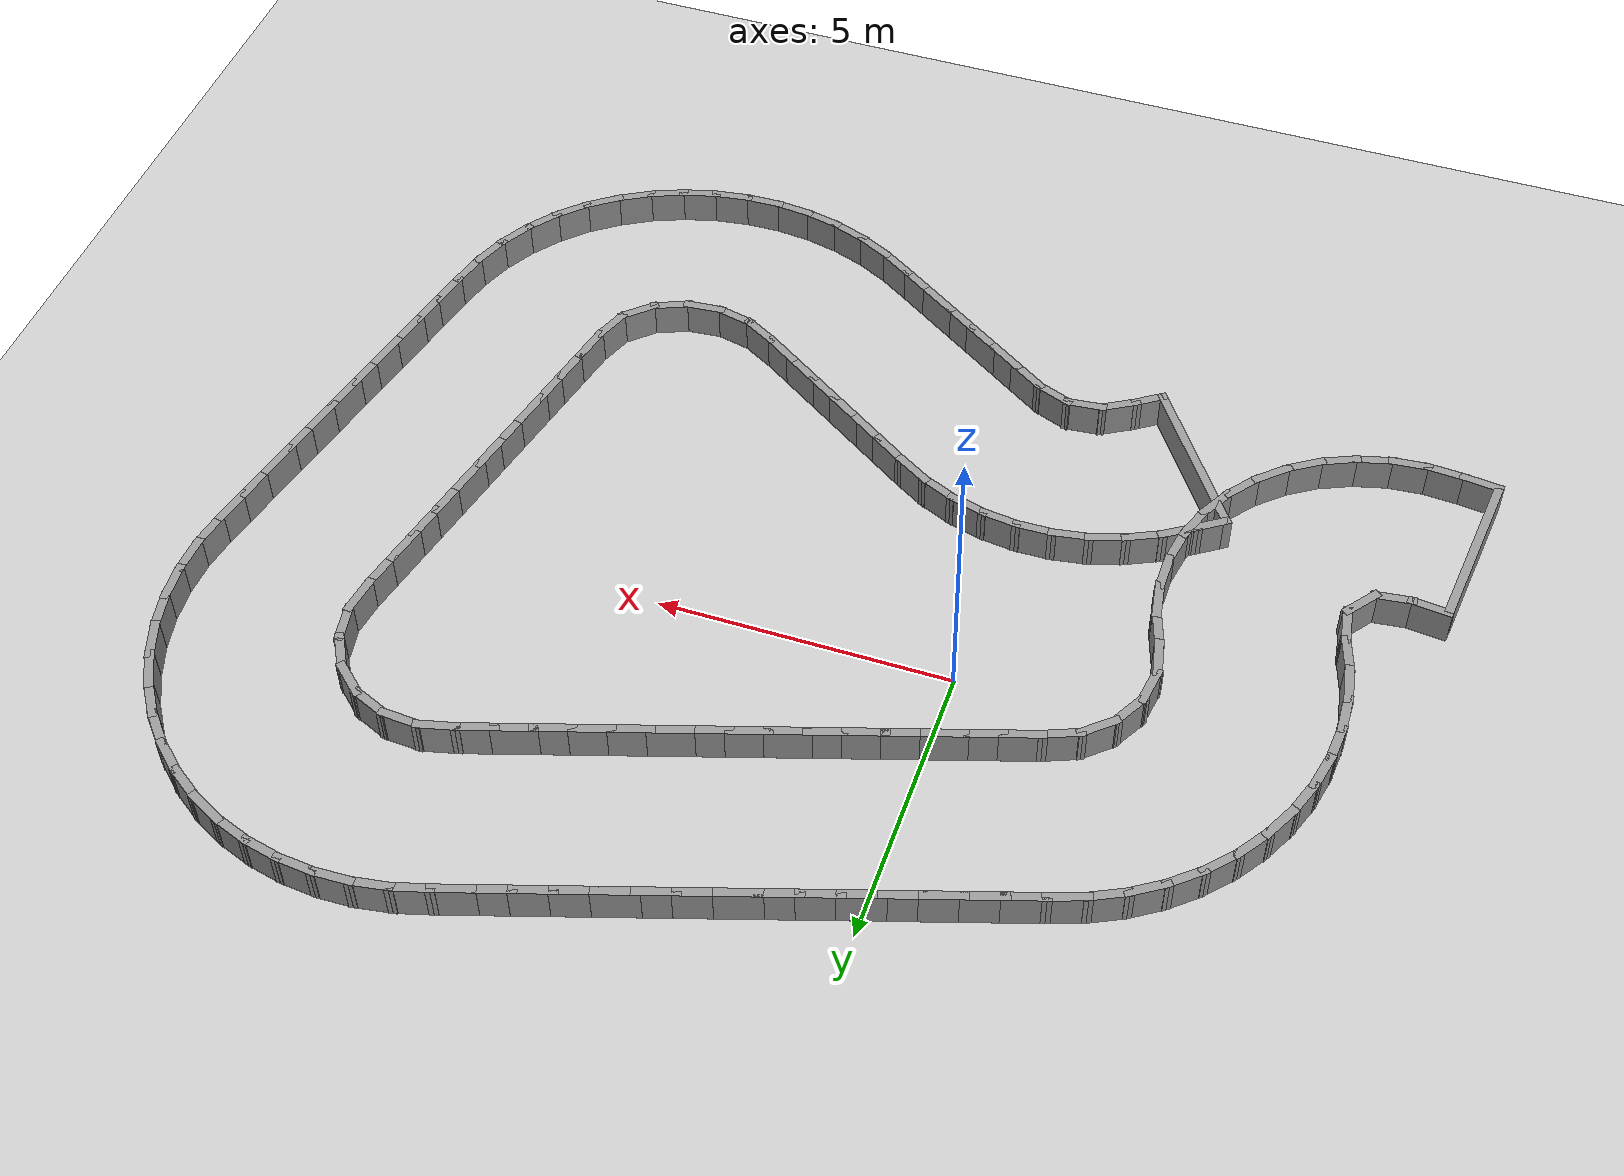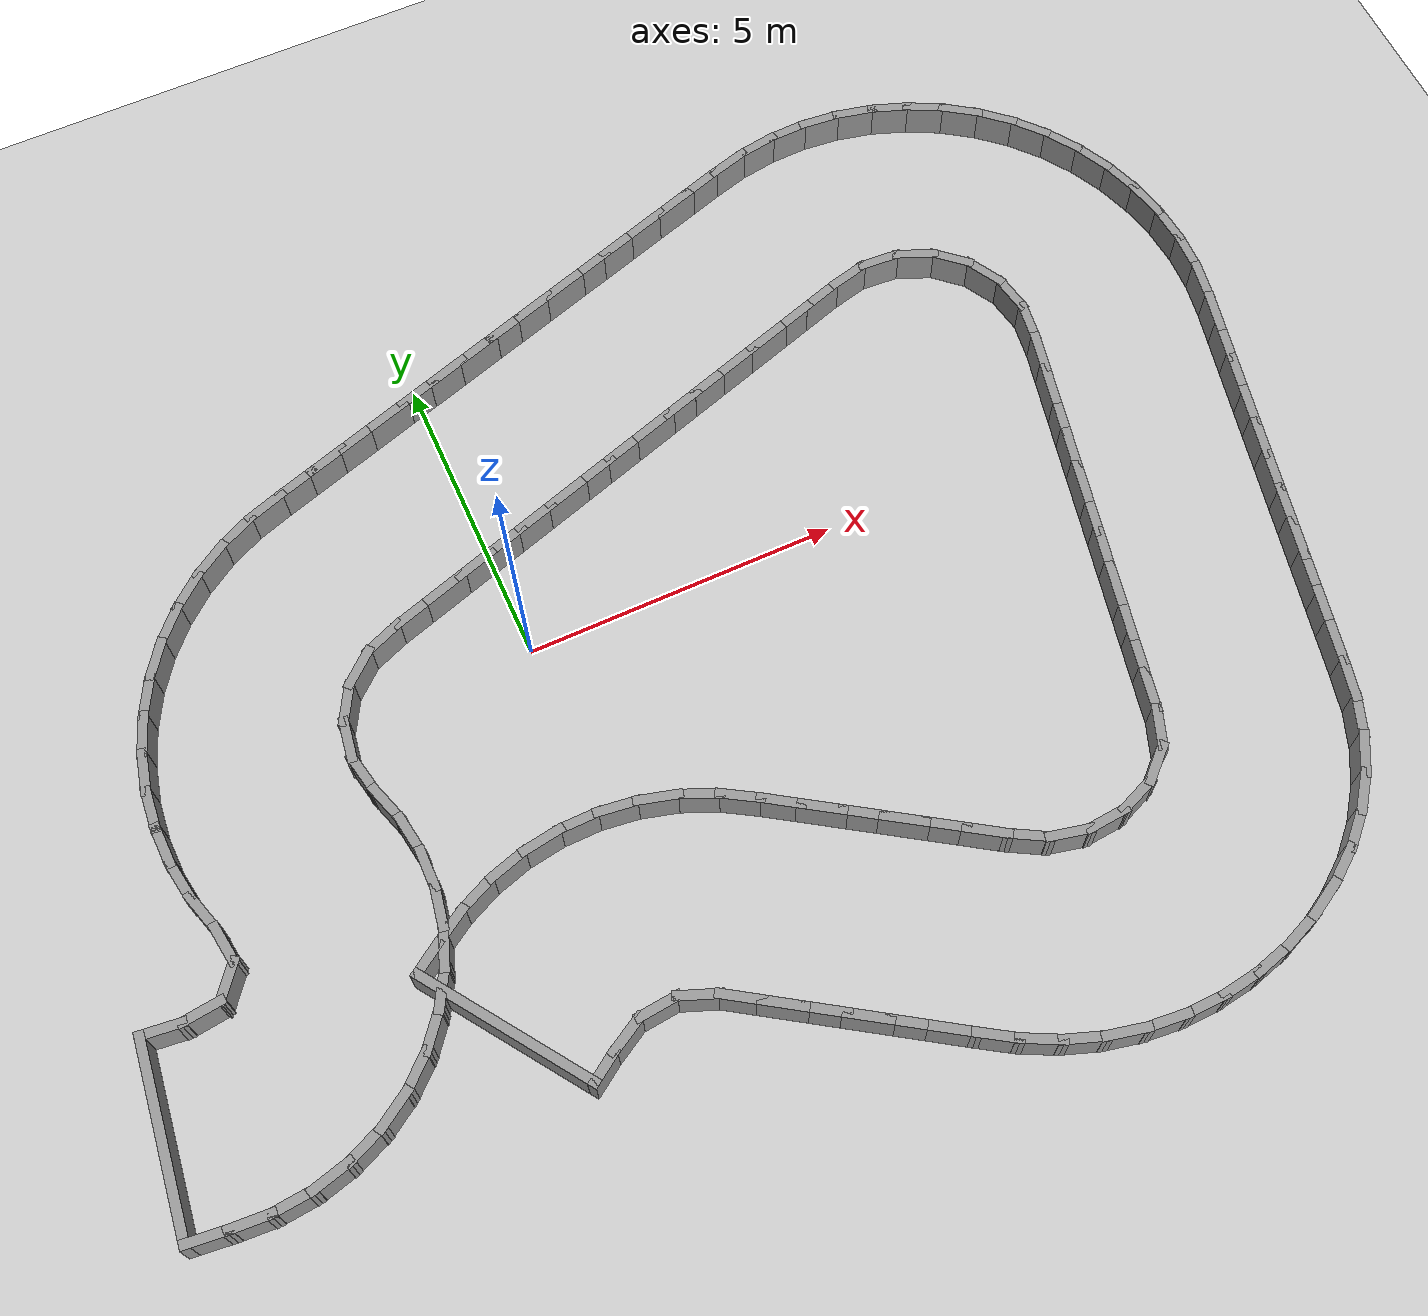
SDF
<?xml version="1.0" ?>
<sdf version='1.7'>
  <world name='default'>
    <plugin name='gazebo_ros_state' filename='libgazebo_ros_state.so'>
      <ros>
        <namespace>/</namespace>
      </ros>
      <update_rate>1000.0</update_rate>
    </plugin>

    <light name='sun' type='directional'>
      <cast_shadows>1</cast_shadows>
      <pose>0 0 10 0 -0 0</pose>
      <diffuse>0.8 0.8 0.8 1</diffuse>
      <specular>0.2 0.2 0.2 1</specular>
      <attenuation>
        <range>1000</range>
        <constant>0.9</constant>
        <linear>0.01</linear>
        <quadratic>0.001</quadratic>
      </attenuation>
      <direction>-0.5 0.1 -0.9</direction>
      <spot>
        <inner_angle>0</inner_angle>
        <outer_angle>0</outer_angle>
        <falloff>0</falloff>
      </spot>
    </light>
    <model name='ground_plane'>
      <static>1</static>
      <link name='link'>
        <collision name='collision'>
          <geometry>
            <plane>
              <normal>0 0 1</normal>
              <size>100 100</size>
            </plane>
          </geometry>
          <surface>
            <friction>
              <ode>
                <mu>100</mu>
                <mu2>50</mu2>
              </ode>
              <torsional>
                <ode/>
              </torsional>
            </friction>
            <contact>
              <ode/>
            </contact>
            <bounce/>
          </surface>
          <max_contacts>10</max_contacts>
        </collision>
        <visual name='visual'>
          <cast_shadows>0</cast_shadows>
          <geometry>
            <plane>
              <normal>0 0 1</normal>
              <size>100 100</size>
            </plane>
          </geometry>
          <material>
            <script>
              <uri>file://media/materials/scripts/gazebo.material</uri>
              <name>Gazebo/Grey</name>
            </script>
          </material>
        </visual>
        <self_collide>0</self_collide>
        <enable_wind>0</enable_wind>
        <kinematic>0</kinematic>
      </link>
    </model>
    <gravity>0 0 -9.8</gravity>
    <magnetic_field>6e-06 2.3e-05 -4.2e-05</magnetic_field>
    <atmosphere type='adiabatic'/>
    <physics type='ode'>
      <max_step_size>0.001</max_step_size>
      <real_time_factor>1</real_time_factor>
      <real_time_update_rate>1000</real_time_update_rate>
    </physics>
    <scene>
      <ambient>0.4 0.4 0.4 1</ambient>
      <background>0.7 0.7 0.7 1</background>
      <shadows>1</shadows>
    </scene>
    <audio>
      <device>default</device>
    </audio>
    <wind/>
    <spherical_coordinates>
      <surface_model>EARTH_WGS84</surface_model>
      <latitude_deg>0</latitude_deg>
      <longitude_deg>0</longitude_deg>
      <elevation>0</elevation>
      <heading_deg>0</heading_deg>
    </spherical_coordinates>
  <model name='rand_turn_12'>
    <pose>0 0 0 0 -0 0</pose>
    <link name='Wall_0'>
      <collision name='Wall_0_Collision'>
        <geometry><box><size>0.7500 0.1500 0.6000</size></box></geometry>
        <pose>0 0 0.3000 0 -0 0</pose>
      </collision>
      <visual name='Wall_0_Visual'>
        <pose>0 0 0.3000 0 -0 0</pose>
        <geometry><box><size>0.7500 0.1500 0.6000</size></box></geometry>
        <material>
          <script>
            <uri>file://media/materials/scripts/gazebo.material</uri>
            <name>Gazebo/Grey</name>
          </script>
          <ambient>1 1 1 1</ambient>
        </material>
      </visual>
      <pose>-6.8772 -3.4257 0 0 -0 -0.11106</pose>
    </link>
    <link name='Wall_1'>
      <collision name='Wall_1_Collision'>
        <geometry><box><size>0.7374 0.1500 0.6000</size></box></geometry>
        <pose>0 0 0.3000 0 -0 0</pose>
      </collision>
      <visual name='Wall_1_Visual'>
        <pose>0 0 0.3000 0 -0 0</pose>
        <geometry><box><size>0.7374 0.1500 0.6000</size></box></geometry>
        <material>
          <script>
            <uri>file://media/materials/scripts/gazebo.material</uri>
            <name>Gazebo/Grey</name>
          </script>
          <ambient>1 1 1 1</ambient>
        </material>
      </visual>
      <pose>-6.2874 -3.4238 0 0 -0 0.11996</pose>
    </link>
    <link name='Wall_2'>
      <collision name='Wall_2_Collision'>
        <geometry><box><size>0.7330 0.1500 0.6000</size></box></geometry>
        <pose>0 0 0.3000 0 -0 0</pose>
      </collision>
      <visual name='Wall_2_Visual'>
        <pose>0 0 0.3000 0 -0 0</pose>
        <geometry><box><size>0.7330 0.1500 0.6000</size></box></geometry>
        <material>
          <script>
            <uri>file://media/materials/scripts/gazebo.material</uri>
            <name>Gazebo/Grey</name>
          </script>
          <ambient>1 1 1 1</ambient>
        </material>
      </visual>
      <pose>-5.8196 -3.1565 0 0 -0 0.92140</pose>
    </link>
    <link name='Wall_3'>
      <collision name='Wall_3_Collision'>
        <geometry><box><size>0.7377 0.1500 0.6000</size></box></geometry>
        <pose>0 0 0.3000 0 -0 0</pose>
      </collision>
      <visual name='Wall_3_Visual'>
        <pose>0 0 0.3000 0 -0 0</pose>
        <geometry><box><size>0.7377 0.1500 0.6000</size></box></geometry>
        <material>
          <script>
            <uri>file://media/materials/scripts/gazebo.material</uri>
            <name>Gazebo/Grey</name>
          </script>
          <ambient>1 1 1 1</ambient>
        </material>
      </visual>
      <pose>-5.6868 -2.6337 0 0 -0 1.71950</pose>
    </link>
    <link name='Wall_4'>
      <collision name='Wall_4_Collision'>
        <geometry><box><size>0.7496 0.1500 0.6000</size></box></geometry>
        <pose>0 0 0.3000 0 -0 0</pose>
      </collision>
      <visual name='Wall_4_Visual'>
        <pose>0 0 0.3000 0 -0 0</pose>
        <geometry><box><size>0.7496 0.1500 0.6000</size></box></geometry>
        <material>
          <script>
            <uri>file://media/materials/scripts/gazebo.material</uri>
            <name>Gazebo/Grey</name>
          </script>
          <ambient>1 1 1 1</ambient>
        </material>
      </visual>
      <pose>-5.8177 -2.0563 0 0 -0 1.86625</pose>
    </link>
    <link name='Wall_5'>
      <collision name='Wall_5_Collision'>
        <geometry><box><size>0.7496 0.1500 0.6000</size></box></geometry>
        <pose>0 0 0.3000 0 -0 0</pose>
      </collision>
      <visual name='Wall_5_Visual'>
        <pose>0 0 0.3000 0 -0 0</pose>
        <geometry><box><size>0.7496 0.1500 0.6000</size></box></geometry>
        <material>
          <script>
            <uri>file://media/materials/scripts/gazebo.material</uri>
            <name>Gazebo/Grey</name>
          </script>
          <ambient>1 1 1 1</ambient>
        </material>
      </visual>
      <pose>-5.9548 -1.4739 0 0 -0 1.73781</pose>
    </link>
    <link name='Wall_6'>
      <collision name='Wall_6_Collision'>
        <geometry><box><size>0.7495 0.1500 0.6000</size></box></geometry>
        <pose>0 0 0.3000 0 -0 0</pose>
      </collision>
      <visual name='Wall_6_Visual'>
        <pose>0 0 0.3000 0 -0 0</pose>
        <geometry><box><size>0.7495 0.1500 0.6000</size></box></geometry>
        <material>
          <script>
            <uri>file://media/materials/scripts/gazebo.material</uri>
            <name>Gazebo/Grey</name>
          </script>
          <ambient>1 1 1 1</ambient>
        </material>
      </visual>
      <pose>-6.0162 -0.8787 0 0 -0 1.60937</pose>
    </link>
    <link name='Wall_7'>
      <collision name='Wall_7_Collision'>
        <geometry><box><size>0.7495 0.1500 0.6000</size></box></geometry>
        <pose>0 0 0.3000 0 -0 0</pose>
      </collision>
      <visual name='Wall_7_Visual'>
        <pose>0 0 0.3000 0 -0 0</pose>
        <geometry><box><size>0.7495 0.1500 0.6000</size></box></geometry>
        <material>
          <script>
            <uri>file://media/materials/scripts/gazebo.material</uri>
            <name>Gazebo/Grey</name>
          </script>
          <ambient>1 1 1 1</ambient>
        </material>
      </visual>
      <pose>-6.0008 -0.2806 0 0 -0 1.48094</pose>
    </link>
    <link name='Wall_8'>
      <collision name='Wall_8_Collision'>
        <geometry><box><size>0.7495 0.1500 0.6000</size></box></geometry>
        <pose>0 0 0.3000 0 -0 0</pose>
      </collision>
      <visual name='Wall_8_Visual'>
        <pose>0 0 0.3000 0 -0 0</pose>
        <geometry><box><size>0.7495 0.1500 0.6000</size></box></geometry>
        <material>
          <script>
            <uri>file://media/materials/scripts/gazebo.material</uri>
            <name>Gazebo/Grey</name>
          </script>
          <ambient>1 1 1 1</ambient>
        </material>
      </visual>
      <pose>-5.9090 0.3106 0 0 -0 1.35250</pose>
    </link>
    <link name='Wall_9'>
      <collision name='Wall_9_Collision'>
        <geometry><box><size>0.7496 0.1500 0.6000</size></box></geometry>
        <pose>0 0 0.3000 0 -0 0</pose>
      </collision>
      <visual name='Wall_9_Visual'>
        <pose>0 0 0.3000 0 -0 0</pose>
        <geometry><box><size>0.7496 0.1500 0.6000</size></box></geometry>
        <material>
          <script>
            <uri>file://media/materials/scripts/gazebo.material</uri>
            <name>Gazebo/Grey</name>
          </script>
          <ambient>1 1 1 1</ambient>
        </material>
      </visual>
      <pose>-5.7422 0.8852 0 0 -0 1.22406</pose>
    </link>
    <link name='Wall_10'>
      <collision name='Wall_10_Collision'>
        <geometry><box><size>0.7496 0.1500 0.6000</size></box></geometry>
        <pose>0 0 0.3000 0 -0 0</pose>
      </collision>
      <visual name='Wall_10_Visual'>
        <pose>0 0 0.3000 0 -0 0</pose>
        <geometry><box><size>0.7496 0.1500 0.6000</size></box></geometry>
        <material>
          <script>
            <uri>file://media/materials/scripts/gazebo.material</uri>
            <name>Gazebo/Grey</name>
          </script>
          <ambient>1 1 1 1</ambient>
        </material>
      </visual>
      <pose>-5.5032 1.4337 0 0 -0 1.09562</pose>
    </link>
    <link name='Wall_11'>
      <collision name='Wall_11_Collision'>
        <geometry><box><size>0.7496 0.1500 0.6000</size></box></geometry>
        <pose>0 0 0.3000 0 -0 0</pose>
      </collision>
      <visual name='Wall_11_Visual'>
        <pose>0 0 0.3000 0 -0 0</pose>
        <geometry><box><size>0.7496 0.1500 0.6000</size></box></geometry>
        <material>
          <script>
            <uri>file://media/materials/scripts/gazebo.material</uri>
            <name>Gazebo/Grey</name>
          </script>
          <ambient>1 1 1 1</ambient>
        </material>
      </visual>
      <pose>-5.1959 1.9471 0 0 -0 0.96718</pose>
    </link>
    <link name='Wall_12'>
      <collision name='Wall_12_Collision'>
        <geometry><box><size>0.7496 0.1500 0.6000</size></box></geometry>
        <pose>0 0 0.3000 0 -0 0</pose>
      </collision>
      <visual name='Wall_12_Visual'>
        <pose>0 0 0.3000 0 -0 0</pose>
        <geometry><box><size>0.7496 0.1500 0.6000</size></box></geometry>
        <material>
          <script>
            <uri>file://media/materials/scripts/gazebo.material</uri>
            <name>Gazebo/Grey</name>
          </script>
          <ambient>1 1 1 1</ambient>
        </material>
      </visual>
      <pose>-4.8252 2.4168 0 0 -0 0.83822</pose>
    </link>
    <link name='Wall_13'>
      <collision name='Wall_13_Collision'>
        <geometry><box><size>0.7496 0.1500 0.6000</size></box></geometry>
        <pose>0 0 0.3000 0 -0 0</pose>
      </collision>
      <visual name='Wall_13_Visual'>
        <pose>0 0 0.3000 0 -0 0</pose>
        <geometry><box><size>0.7496 0.1500 0.6000</size></box></geometry>
        <material>
          <script>
            <uri>file://media/materials/scripts/gazebo.material</uri>
            <name>Gazebo/Grey</name>
          </script>
          <ambient>1 1 1 1</ambient>
        </material>
      </visual>
      <pose>-4.3973 2.8350 0 0 -0 0.70952</pose>
    </link>
    <link name='Wall_14'>
      <collision name='Wall_14_Collision'>
        <geometry><box><size>0.7496 0.1500 0.6000</size></box></geometry>
        <pose>0 0 0.3000 0 -0 0</pose>
      </collision>
      <visual name='Wall_14_Visual'>
        <pose>0 0 0.3000 0 -0 0</pose>
        <geometry><box><size>0.7496 0.1500 0.6000</size></box></geometry>
        <material>
          <script>
            <uri>file://media/materials/scripts/gazebo.material</uri>
            <name>Gazebo/Grey</name>
          </script>
          <ambient>1 1 1 1</ambient>
        </material>
      </visual>
      <pose>-3.9192 3.1948 0 0 -0 0.58108</pose>
    </link>
    <link name='Wall_15'>
      <collision name='Wall_15_Collision'>
        <geometry><box><size>0.7495 0.1500 0.6000</size></box></geometry>
        <pose>0 0 0.3000 0 -0 0</pose>
      </collision>
      <visual name='Wall_15_Visual'>
        <pose>0 0 0.3000 0 -0 0</pose>
        <geometry><box><size>0.7495 0.1500 0.6000</size></box></geometry>
        <material>
          <script>
            <uri>file://media/materials/scripts/gazebo.material</uri>
            <name>Gazebo/Grey</name>
          </script>
          <ambient>1 1 1 1</ambient>
        </material>
      </visual>
      <pose>-3.3991 3.4905 0 0 -0 0.45264</pose>
    </link>
    <link name='Wall_16'>
      <collision name='Wall_16_Collision'>
        <geometry><box><size>0.7498 0.1500 0.6000</size></box></geometry>
        <pose>0 0 0.3000 0 -0 0</pose>
      </collision>
      <visual name='Wall_16_Visual'>
        <pose>0 0 0.3000 0 -0 0</pose>
        <geometry><box><size>0.7498 0.1500 0.6000</size></box></geometry>
        <material>
          <script>
            <uri>file://media/materials/scripts/gazebo.material</uri>
            <name>Gazebo/Grey</name>
          </script>
          <ambient>1 1 1 1</ambient>
        </material>
      </visual>
      <pose>-2.8460 3.7194 0 0 -0 0.33208</pose>
    </link>
    <link name='Wall_17'>
      <collision name='Wall_17_Collision'>
        <geometry><box><size>0.7500 0.1500 0.6000</size></box></geometry>
        <pose>0 0 0.3000 0 -0 0</pose>
      </collision>
      <visual name='Wall_17_Visual'>
        <pose>0 0 0.3000 0 -0 0</pose>
        <geometry><box><size>0.7500 0.1500 0.6000</size></box></geometry>
        <material>
          <script>
            <uri>file://media/materials/scripts/gazebo.material</uri>
            <name>Gazebo/Grey</name>
          </script>
          <ambient>1 1 1 1</ambient>
        </material>
      </visual>
      <pose>-2.2767 3.9083 0 0 -0 0.30859</pose>
    </link>
    <link name='Wall_18'>
      <collision name='Wall_18_Collision'>
        <geometry><box><size>0.7500 0.1500 0.6000</size></box></geometry>
        <pose>0 0 0.3000 0 -0 0</pose>
      </collision>
      <visual name='Wall_18_Visual'>
        <pose>0 0 0.3000 0 -0 0</pose>
        <geometry><box><size>0.7500 0.1500 0.6000</size></box></geometry>
        <material>
          <script>
            <uri>file://media/materials/scripts/gazebo.material</uri>
            <name>Gazebo/Grey</name>
          </script>
          <ambient>1 1 1 1</ambient>
        </material>
      </visual>
      <pose>-1.7050 4.0905 0 0 -0 0.30859</pose>
    </link>
    <link name='Wall_19'>
      <collision name='Wall_19_Collision'>
        <geometry><box><size>0.7500 0.1500 0.6000</size></box></geometry>
        <pose>0 0 0.3000 0 -0 0</pose>
      </collision>
      <visual name='Wall_19_Visual'>
        <pose>0 0 0.3000 0 -0 0</pose>
        <geometry><box><size>0.7500 0.1500 0.6000</size></box></geometry>
        <material>
          <script>
            <uri>file://media/materials/scripts/gazebo.material</uri>
            <name>Gazebo/Grey</name>
          </script>
          <ambient>1 1 1 1</ambient>
        </material>
      </visual>
      <pose>-1.1334 4.2727 0 0 -0 0.30859</pose>
    </link>
    <link name='Wall_20'>
      <collision name='Wall_20_Collision'>
        <geometry><box><size>0.7500 0.1500 0.6000</size></box></geometry>
        <pose>0 0 0.3000 0 -0 0</pose>
      </collision>
      <visual name='Wall_20_Visual'>
        <pose>0 0 0.3000 0 -0 0</pose>
        <geometry><box><size>0.7500 0.1500 0.6000</size></box></geometry>
        <material>
          <script>
            <uri>file://media/materials/scripts/gazebo.material</uri>
            <name>Gazebo/Grey</name>
          </script>
          <ambient>1 1 1 1</ambient>
        </material>
      </visual>
      <pose>-0.5617 4.4549 0 0 -0 0.30859</pose>
    </link>
    <link name='Wall_21'>
      <collision name='Wall_21_Collision'>
        <geometry><box><size>0.7500 0.1500 0.6000</size></box></geometry>
        <pose>0 0 0.3000 0 -0 0</pose>
      </collision>
      <visual name='Wall_21_Visual'>
        <pose>0 0 0.3000 0 -0 0</pose>
        <geometry><box><size>0.7500 0.1500 0.6000</size></box></geometry>
        <material>
          <script>
            <uri>file://media/materials/scripts/gazebo.material</uri>
            <name>Gazebo/Grey</name>
          </script>
          <ambient>1 1 1 1</ambient>
        </material>
      </visual>
      <pose>0.0099 4.6372 0 0 -0 0.30859</pose>
    </link>
    <link name='Wall_22'>
      <collision name='Wall_22_Collision'>
        <geometry><box><size>0.7500 0.1500 0.6000</size></box></geometry>
        <pose>0 0 0.3000 0 -0 0</pose>
      </collision>
      <visual name='Wall_22_Visual'>
        <pose>0 0 0.3000 0 -0 0</pose>
        <geometry><box><size>0.7500 0.1500 0.6000</size></box></geometry>
        <material>
          <script>
            <uri>file://media/materials/scripts/gazebo.material</uri>
            <name>Gazebo/Grey</name>
          </script>
          <ambient>1 1 1 1</ambient>
        </material>
      </visual>
      <pose>0.5816 4.8194 0 0 -0 0.30859</pose>
    </link>
    <link name='Wall_23'>
      <collision name='Wall_23_Collision'>
        <geometry><box><size>0.7500 0.1500 0.6000</size></box></geometry>
        <pose>0 0 0.3000 0 -0 0</pose>
      </collision>
      <visual name='Wall_23_Visual'>
        <pose>0 0 0.3000 0 -0 0</pose>
        <geometry><box><size>0.7500 0.1500 0.6000</size></box></geometry>
        <material>
          <script>
            <uri>file://media/materials/scripts/gazebo.material</uri>
            <name>Gazebo/Grey</name>
          </script>
          <ambient>1 1 1 1</ambient>
        </material>
      </visual>
      <pose>1.1533 5.0016 0 0 -0 0.30859</pose>
    </link>
    <link name='Wall_24'>
      <collision name='Wall_24_Collision'>
        <geometry><box><size>0.7500 0.1500 0.6000</size></box></geometry>
        <pose>0 0 0.3000 0 -0 0</pose>
      </collision>
      <visual name='Wall_24_Visual'>
        <pose>0 0 0.3000 0 -0 0</pose>
        <geometry><box><size>0.7500 0.1500 0.6000</size></box></geometry>
        <material>
          <script>
            <uri>file://media/materials/scripts/gazebo.material</uri>
            <name>Gazebo/Grey</name>
          </script>
          <ambient>1 1 1 1</ambient>
        </material>
      </visual>
      <pose>1.7249 5.1839 0 0 -0 0.30859</pose>
    </link>
    <link name='Wall_25'>
      <collision name='Wall_25_Collision'>
        <geometry><box><size>0.7500 0.1500 0.6000</size></box></geometry>
        <pose>0 0 0.3000 0 -0 0</pose>
      </collision>
      <visual name='Wall_25_Visual'>
        <pose>0 0 0.3000 0 -0 0</pose>
        <geometry><box><size>0.7500 0.1500 0.6000</size></box></geometry>
        <material>
          <script>
            <uri>file://media/materials/scripts/gazebo.material</uri>
            <name>Gazebo/Grey</name>
          </script>
          <ambient>1 1 1 1</ambient>
        </material>
      </visual>
      <pose>2.2966 5.3661 0 0 -0 0.30859</pose>
    </link>
    <link name='Wall_26'>
      <collision name='Wall_26_Collision'>
        <geometry><box><size>0.7500 0.1500 0.6000</size></box></geometry>
        <pose>0 0 0.3000 0 -0 0</pose>
      </collision>
      <visual name='Wall_26_Visual'>
        <pose>0 0 0.3000 0 -0 0</pose>
        <geometry><box><size>0.7500 0.1500 0.6000</size></box></geometry>
        <material>
          <script>
            <uri>file://media/materials/scripts/gazebo.material</uri>
            <name>Gazebo/Grey</name>
          </script>
          <ambient>1 1 1 1</ambient>
        </material>
      </visual>
      <pose>2.8682 5.5483 0 0 -0 0.30859</pose>
    </link>
    <link name='Wall_27'>
      <collision name='Wall_27_Collision'>
        <geometry><box><size>0.7500 0.1500 0.6000</size></box></geometry>
        <pose>0 0 0.3000 0 -0 0</pose>
      </collision>
      <visual name='Wall_27_Visual'>
        <pose>0 0 0.3000 0 -0 0</pose>
        <geometry><box><size>0.7500 0.1500 0.6000</size></box></geometry>
        <material>
          <script>
            <uri>file://media/materials/scripts/gazebo.material</uri>
            <name>Gazebo/Grey</name>
          </script>
          <ambient>1 1 1 1</ambient>
        </material>
      </visual>
      <pose>3.4399 5.7306 0 0 -0 0.30859</pose>
    </link>
    <link name='Wall_28'>
      <collision name='Wall_28_Collision'>
        <geometry><box><size>0.7500 0.1500 0.6000</size></box></geometry>
        <pose>0 0 0.3000 0 -0 0</pose>
      </collision>
      <visual name='Wall_28_Visual'>
        <pose>0 0 0.3000 0 -0 0</pose>
        <geometry><box><size>0.7500 0.1500 0.6000</size></box></geometry>
        <material>
          <script>
            <uri>file://media/materials/scripts/gazebo.material</uri>
            <name>Gazebo/Grey</name>
          </script>
          <ambient>1 1 1 1</ambient>
        </material>
      </visual>
      <pose>4.0115 5.9128 0 0 -0 0.30859</pose>
    </link>
    <link name='Wall_29'>
      <collision name='Wall_29_Collision'>
        <geometry><box><size>0.7500 0.1500 0.6000</size></box></geometry>
        <pose>0 0 0.3000 0 -0 0</pose>
      </collision>
      <visual name='Wall_29_Visual'>
        <pose>0 0 0.3000 0 -0 0</pose>
        <geometry><box><size>0.7500 0.1500 0.6000</size></box></geometry>
        <material>
          <script>
            <uri>file://media/materials/scripts/gazebo.material</uri>
            <name>Gazebo/Grey</name>
          </script>
          <ambient>1 1 1 1</ambient>
        </material>
      </visual>
      <pose>4.5832 6.0950 0 0 -0 0.30859</pose>
    </link>
    <link name='Wall_30'>
      <collision name='Wall_30_Collision'>
        <geometry><box><size>0.7500 0.1500 0.6000</size></box></geometry>
        <pose>0 0 0.3000 0 -0 0</pose>
      </collision>
      <visual name='Wall_30_Visual'>
        <pose>0 0 0.3000 0 -0 0</pose>
        <geometry><box><size>0.7500 0.1500 0.6000</size></box></geometry>
        <material>
          <script>
            <uri>file://media/materials/scripts/gazebo.material</uri>
            <name>Gazebo/Grey</name>
          </script>
          <ambient>1 1 1 1</ambient>
        </material>
      </visual>
      <pose>5.1549 6.2772 0 0 -0 0.30859</pose>
    </link>
    <link name='Wall_31'>
      <collision name='Wall_31_Collision'>
        <geometry><box><size>0.7500 0.1500 0.6000</size></box></geometry>
        <pose>0 0 0.3000 0 -0 0</pose>
      </collision>
      <visual name='Wall_31_Visual'>
        <pose>0 0 0.3000 0 -0 0</pose>
        <geometry><box><size>0.7500 0.1500 0.6000</size></box></geometry>
        <material>
          <script>
            <uri>file://media/materials/scripts/gazebo.material</uri>
            <name>Gazebo/Grey</name>
          </script>
          <ambient>1 1 1 1</ambient>
        </material>
      </visual>
      <pose>5.7265 6.4595 0 0 -0 0.30859</pose>
    </link>
    <link name='Wall_32'>
      <collision name='Wall_32_Collision'>
        <geometry><box><size>0.7497 0.1500 0.6000</size></box></geometry>
        <pose>0 0 0.3000 0 -0 0</pose>
      </collision>
      <visual name='Wall_32_Visual'>
        <pose>0 0 0.3000 0 -0 0</pose>
        <geometry><box><size>0.7497 0.1500 0.6000</size></box></geometry>
        <material>
          <script>
            <uri>file://media/materials/scripts/gazebo.material</uri>
            <name>Gazebo/Grey</name>
          </script>
          <ambient>1 1 1 1</ambient>
        </material>
      </visual>
      <pose>6.3008 6.6327 0 0 -0 0.27745</pose>
    </link>
    <link name='Wall_33'>
      <collision name='Wall_33_Collision'>
        <geometry><box><size>0.7496 0.1500 0.6000</size></box></geometry>
        <pose>0 0 0.3000 0 -0 0</pose>
      </collision>
      <visual name='Wall_33_Visual'>
        <pose>0 0 0.3000 0 -0 0</pose>
        <geometry><box><size>0.7496 0.1500 0.6000</size></box></geometry>
        <material>
          <script>
            <uri>file://media/materials/scripts/gazebo.material</uri>
            <name>Gazebo/Grey</name>
          </script>
          <ambient>1 1 1 1</ambient>
        </material>
      </visual>
      <pose>6.8852 6.7620 0 0 -0 0.15782</pose>
    </link>
    <link name='Wall_34'>
      <collision name='Wall_34_Collision'>
        <geometry><box><size>0.7496 0.1500 0.6000</size></box></geometry>
        <pose>0 0 0.3000 0 -0 0</pose>
      </collision>
      <visual name='Wall_34_Visual'>
        <pose>0 0 0.3000 0 -0 0</pose>
        <geometry><box><size>0.7496 0.1500 0.6000</size></box></geometry>
        <material>
          <script>
            <uri>file://media/materials/scripts/gazebo.material</uri>
            <name>Gazebo/Grey</name>
          </script>
          <ambient>1 1 1 1</ambient>
        </material>
      </visual>
      <pose>7.4810 6.8185 0 0 -0 0.03142</pose>
    </link>
    <link name='Wall_35'>
      <collision name='Wall_35_Collision'>
        <geometry><box><size>0.7496 0.1500 0.6000</size></box></geometry>
        <pose>0 0 0.3000 0 -0 0</pose>
      </collision>
      <visual name='Wall_35_Visual'>
        <pose>0 0 0.3000 0 -0 0</pose>
        <geometry><box><size>0.7496 0.1500 0.6000</size></box></geometry>
        <material>
          <script>
            <uri>file://media/materials/scripts/gazebo.material</uri>
            <name>Gazebo/Grey</name>
          </script>
          <ambient>1 1 1 1</ambient>
        </material>
      </visual>
      <pose>8.0791 6.7997 0 0 -0 -0.09425</pose>
    </link>
    <link name='Wall_36'>
      <collision name='Wall_36_Collision'>
        <geometry><box><size>0.7496 0.1500 0.6000</size></box></geometry>
        <pose>0 0 0.3000 0 -0 0</pose>
      </collision>
      <visual name='Wall_36_Visual'>
        <pose>0 0 0.3000 0 -0 0</pose>
        <geometry><box><size>0.7496 0.1500 0.6000</size></box></geometry>
        <material>
          <script>
            <uri>file://media/materials/scripts/gazebo.material</uri>
            <name>Gazebo/Grey</name>
          </script>
          <ambient>1 1 1 1</ambient>
        </material>
      </visual>
      <pose>8.6701 6.7061 0 0 -0 -0.21991</pose>
    </link>
    <link name='Wall_37'>
      <collision name='Wall_37_Collision'>
        <geometry><box><size>0.7496 0.1500 0.6000</size></box></geometry>
        <pose>0 0 0.3000 0 -0 0</pose>
      </collision>
      <visual name='Wall_37_Visual'>
        <pose>0 0 0.3000 0 -0 0</pose>
        <geometry><box><size>0.7496 0.1500 0.6000</size></box></geometry>
        <material>
          <script>
            <uri>file://media/materials/scripts/gazebo.material</uri>
            <name>Gazebo/Grey</name>
          </script>
          <ambient>1 1 1 1</ambient>
        </material>
      </visual>
      <pose>9.2447 6.5392 0 0 -0 -0.34558</pose>
    </link>
    <link name='Wall_38'>
      <collision name='Wall_38_Collision'>
        <geometry><box><size>0.7496 0.1500 0.6000</size></box></geometry>
        <pose>0 0 0.3000 0 -0 0</pose>
      </collision>
      <visual name='Wall_38_Visual'>
        <pose>0 0 0.3000 0 -0 0</pose>
        <geometry><box><size>0.7496 0.1500 0.6000</size></box></geometry>
        <material>
          <script>
            <uri>file://media/materials/scripts/gazebo.material</uri>
            <name>Gazebo/Grey</name>
          </script>
          <ambient>1 1 1 1</ambient>
        </material>
      </visual>
      <pose>9.7939 6.3015 0 0 -0 -0.47124</pose>
    </link>
    <link name='Wall_39'>
      <collision name='Wall_39_Collision'>
        <geometry><box><size>0.7496 0.1500 0.6000</size></box></geometry>
        <pose>0 0 0.3000 0 -0 0</pose>
      </collision>
      <visual name='Wall_39_Visual'>
        <pose>0 0 0.3000 0 -0 0</pose>
        <geometry><box><size>0.7496 0.1500 0.6000</size></box></geometry>
        <material>
          <script>
            <uri>file://media/materials/scripts/gazebo.material</uri>
            <name>Gazebo/Grey</name>
          </script>
          <ambient>1 1 1 1</ambient>
        </material>
      </visual>
      <pose>10.3090 5.9969 0 0 -0 -0.59690</pose>
    </link>
    <link name='Wall_40'>
      <collision name='Wall_40_Collision'>
        <geometry><box><size>0.7496 0.1500 0.6000</size></box></geometry>
        <pose>0 0 0.3000 0 -0 0</pose>
      </collision>
      <visual name='Wall_40_Visual'>
        <pose>0 0 0.3000 0 -0 0</pose>
        <geometry><box><size>0.7496 0.1500 0.6000</size></box></geometry>
        <material>
          <script>
            <uri>file://media/materials/scripts/gazebo.material</uri>
            <name>Gazebo/Grey</name>
          </script>
          <ambient>1 1 1 1</ambient>
        </material>
      </visual>
      <pose>10.7817 5.6301 0 0 -0 -0.72289</pose>
    </link>
    <link name='Wall_41'>
      <collision name='Wall_41_Collision'>
        <geometry><box><size>0.7496 0.1500 0.6000</size></box></geometry>
        <pose>0 0 0.3000 0 -0 0</pose>
      </collision>
      <visual name='Wall_41_Visual'>
        <pose>0 0 0.3000 0 -0 0</pose>
        <geometry><box><size>0.7496 0.1500 0.6000</size></box></geometry>
        <material>
          <script>
            <uri>file://media/materials/scripts/gazebo.material</uri>
            <name>Gazebo/Grey</name>
          </script>
          <ambient>1 1 1 1</ambient>
        </material>
      </visual>
      <pose>11.2046 5.2066 0 0 -0 -0.84928</pose>
    </link>
    <link name='Wall_42'>
      <collision name='Wall_42_Collision'>
        <geometry><box><size>0.7496 0.1500 0.6000</size></box></geometry>
        <pose>0 0 0.3000 0 -0 0</pose>
      </collision>
      <visual name='Wall_42_Visual'>
        <pose>0 0 0.3000 0 -0 0</pose>
        <geometry><box><size>0.7496 0.1500 0.6000</size></box></geometry>
        <material>
          <script>
            <uri>file://media/materials/scripts/gazebo.material</uri>
            <name>Gazebo/Grey</name>
          </script>
          <ambient>1 1 1 1</ambient>
        </material>
      </visual>
      <pose>11.5708 4.7334 0 0 -0 -0.97494</pose>
    </link>
    <link name='Wall_43'>
      <collision name='Wall_43_Collision'>
        <geometry><box><size>0.7496 0.1500 0.6000</size></box></geometry>
        <pose>0 0 0.3000 0 -0 0</pose>
      </collision>
      <visual name='Wall_43_Visual'>
        <pose>0 0 0.3000 0 -0 0</pose>
        <geometry><box><size>0.7496 0.1500 0.6000</size></box></geometry>
        <material>
          <script>
            <uri>file://media/materials/scripts/gazebo.material</uri>
            <name>Gazebo/Grey</name>
          </script>
          <ambient>1 1 1 1</ambient>
        </material>
      </visual>
      <pose>11.8749 4.2180 0 0 -0 -1.10061</pose>
    </link>
    <link name='Wall_44'>
      <collision name='Wall_44_Collision'>
        <geometry><box><size>0.7496 0.1500 0.6000</size></box></geometry>
        <pose>0 0 0.3000 0 -0 0</pose>
      </collision>
      <visual name='Wall_44_Visual'>
        <pose>0 0 0.3000 0 -0 0</pose>
        <geometry><box><size>0.7496 0.1500 0.6000</size></box></geometry>
        <material>
          <script>
            <uri>file://media/materials/scripts/gazebo.material</uri>
            <name>Gazebo/Grey</name>
          </script>
          <ambient>1 1 1 1</ambient>
        </material>
      </visual>
      <pose>12.1120 3.6686 0 0 -0 -1.22627</pose>
    </link>
    <link name='Wall_45'>
      <collision name='Wall_45_Collision'>
        <geometry><box><size>0.7496 0.1500 0.6000</size></box></geometry>
        <pose>0 0 0.3000 0 -0 0</pose>
      </collision>
      <visual name='Wall_45_Visual'>
        <pose>0 0 0.3000 0 -0 0</pose>
        <geometry><box><size>0.7496 0.1500 0.6000</size></box></geometry>
        <material>
          <script>
            <uri>file://media/materials/scripts/gazebo.material</uri>
            <name>Gazebo/Grey</name>
          </script>
          <ambient>1 1 1 1</ambient>
        </material>
      </visual>
      <pose>12.2783 3.0938 0 0 -0 -1.35194</pose>
    </link>
    <link name='Wall_46'>
      <collision name='Wall_46_Collision'>
        <geometry><box><size>0.7496 0.1500 0.6000</size></box></geometry>
        <pose>0 0 0.3000 0 -0 0</pose>
      </collision>
      <visual name='Wall_46_Visual'>
        <pose>0 0 0.3000 0 -0 0</pose>
        <geometry><box><size>0.7496 0.1500 0.6000</size></box></geometry>
        <material>
          <script>
            <uri>file://media/materials/scripts/gazebo.material</uri>
            <name>Gazebo/Grey</name>
          </script>
          <ambient>1 1 1 1</ambient>
        </material>
      </visual>
      <pose>12.3713 2.5027 0 0 -0 -1.47760</pose>
    </link>
    <link name='Wall_47'>
      <collision name='Wall_47_Collision'>
        <geometry><box><size>0.7496 0.1500 0.6000</size></box></geometry>
        <pose>0 0 0.3000 0 -0 0</pose>
      </collision>
      <visual name='Wall_47_Visual'>
        <pose>0 0 0.3000 0 -0 0</pose>
        <geometry><box><size>0.7496 0.1500 0.6000</size></box></geometry>
        <material>
          <script>
            <uri>file://media/materials/scripts/gazebo.material</uri>
            <name>Gazebo/Grey</name>
          </script>
          <ambient>1 1 1 1</ambient>
        </material>
      </visual>
      <pose>12.3894 1.9046 0 0 -0 -1.60360</pose>
    </link>
    <link name='Wall_48'>
      <collision name='Wall_48_Collision'>
        <geometry><box><size>0.7496 0.1500 0.6000</size></box></geometry>
        <pose>0 0 0.3000 0 -0 0</pose>
      </collision>
      <visual name='Wall_48_Visual'>
        <pose>0 0 0.3000 0 -0 0</pose>
        <geometry><box><size>0.7496 0.1500 0.6000</size></box></geometry>
        <material>
          <script>
            <uri>file://media/materials/scripts/gazebo.material</uri>
            <name>Gazebo/Grey</name>
          </script>
          <ambient>1 1 1 1</ambient>
        </material>
      </visual>
      <pose>12.3318 1.3089 0 0 -0 -1.73055</pose>
    </link>
    <link name='Wall_49'>
      <collision name='Wall_49_Collision'>
        <geometry><box><size>0.7500 0.1500 0.6000</size></box></geometry>
        <pose>0 0 0.3000 0 -0 0</pose>
      </collision>
      <visual name='Wall_49_Visual'>
        <pose>0 0 0.3000 0 -0 0</pose>
        <geometry><box><size>0.7500 0.1500 0.6000</size></box></geometry>
        <material>
          <script>
            <uri>file://media/materials/scripts/gazebo.material</uri>
            <name>Gazebo/Grey</name>
          </script>
          <ambient>1 1 1 1</ambient>
        </material>
      </visual>
      <pose>12.2216 0.7196 0 0 -0 -1.78095</pose>
    </link>
    <link name='Wall_50'>
      <collision name='Wall_50_Collision'>
        <geometry><box><size>0.7500 0.1500 0.6000</size></box></geometry>
        <pose>0 0 0.3000 0 -0 0</pose>
      </collision>
      <visual name='Wall_50_Visual'>
        <pose>0 0 0.3000 0 -0 0</pose>
        <geometry><box><size>0.7500 0.1500 0.6000</size></box></geometry>
        <material>
          <script>
            <uri>file://media/materials/scripts/gazebo.material</uri>
            <name>Gazebo/Grey</name>
          </script>
          <ambient>1 1 1 1</ambient>
        </material>
      </visual>
      <pose>12.0964 0.1328 0 0 -0 -1.78095</pose>
    </link>
    <link name='Wall_51'>
      <collision name='Wall_51_Collision'>
        <geometry><box><size>0.7500 0.1500 0.6000</size></box></geometry>
        <pose>0 0 0.3000 0 -0 0</pose>
      </collision>
      <visual name='Wall_51_Visual'>
        <pose>0 0 0.3000 0 -0 0</pose>
        <geometry><box><size>0.7500 0.1500 0.6000</size></box></geometry>
        <material>
          <script>
            <uri>file://media/materials/scripts/gazebo.material</uri>
            <name>Gazebo/Grey</name>
          </script>
          <ambient>1 1 1 1</ambient>
        </material>
      </visual>
      <pose>11.9712 -0.4540 0 0 -0 -1.78095</pose>
    </link>
    <link name='Wall_52'>
      <collision name='Wall_52_Collision'>
        <geometry><box><size>0.7500 0.1500 0.6000</size></box></geometry>
        <pose>0 0 0.3000 0 -0 0</pose>
      </collision>
      <visual name='Wall_52_Visual'>
        <pose>0 0 0.3000 0 -0 0</pose>
        <geometry><box><size>0.7500 0.1500 0.6000</size></box></geometry>
        <material>
          <script>
            <uri>file://media/materials/scripts/gazebo.material</uri>
            <name>Gazebo/Grey</name>
          </script>
          <ambient>1 1 1 1</ambient>
        </material>
      </visual>
      <pose>11.8461 -1.0408 0 0 -0 -1.78095</pose>
    </link>
    <link name='Wall_53'>
      <collision name='Wall_53_Collision'>
        <geometry><box><size>0.7500 0.1500 0.6000</size></box></geometry>
        <pose>0 0 0.3000 0 -0 0</pose>
      </collision>
      <visual name='Wall_53_Visual'>
        <pose>0 0 0.3000 0 -0 0</pose>
        <geometry><box><size>0.7500 0.1500 0.6000</size></box></geometry>
        <material>
          <script>
            <uri>file://media/materials/scripts/gazebo.material</uri>
            <name>Gazebo/Grey</name>
          </script>
          <ambient>1 1 1 1</ambient>
        </material>
      </visual>
      <pose>11.7209 -1.6276 0 0 -0 -1.78095</pose>
    </link>
    <link name='Wall_54'>
      <collision name='Wall_54_Collision'>
        <geometry><box><size>0.7500 0.1500 0.6000</size></box></geometry>
        <pose>0 0 0.3000 0 -0 0</pose>
      </collision>
      <visual name='Wall_54_Visual'>
        <pose>0 0 0.3000 0 -0 0</pose>
        <geometry><box><size>0.7500 0.1500 0.6000</size></box></geometry>
        <material>
          <script>
            <uri>file://media/materials/scripts/gazebo.material</uri>
            <name>Gazebo/Grey</name>
          </script>
          <ambient>1 1 1 1</ambient>
        </material>
      </visual>
      <pose>11.5957 -2.2144 0 0 -0 -1.78095</pose>
    </link>
    <link name='Wall_55'>
      <collision name='Wall_55_Collision'>
        <geometry><box><size>0.7500 0.1500 0.6000</size></box></geometry>
        <pose>0 0 0.3000 0 -0 0</pose>
      </collision>
      <visual name='Wall_55_Visual'>
        <pose>0 0 0.3000 0 -0 0</pose>
        <geometry><box><size>0.7500 0.1500 0.6000</size></box></geometry>
        <material>
          <script>
            <uri>file://media/materials/scripts/gazebo.material</uri>
            <name>Gazebo/Grey</name>
          </script>
          <ambient>1 1 1 1</ambient>
        </material>
      </visual>
      <pose>11.4706 -2.8012 0 0 -0 -1.78095</pose>
    </link>
    <link name='Wall_56'>
      <collision name='Wall_56_Collision'>
        <geometry><box><size>0.7500 0.1500 0.6000</size></box></geometry>
        <pose>0 0 0.3000 0 -0 0</pose>
      </collision>
      <visual name='Wall_56_Visual'>
        <pose>0 0 0.3000 0 -0 0</pose>
        <geometry><box><size>0.7500 0.1500 0.6000</size></box></geometry>
        <material>
          <script>
            <uri>file://media/materials/scripts/gazebo.material</uri>
            <name>Gazebo/Grey</name>
          </script>
          <ambient>1 1 1 1</ambient>
        </material>
      </visual>
      <pose>11.3454 -3.3880 0 0 -0 -1.78095</pose>
    </link>
    <link name='Wall_57'>
      <collision name='Wall_57_Collision'>
        <geometry><box><size>0.7500 0.1500 0.6000</size></box></geometry>
        <pose>0 0 0.3000 0 -0 0</pose>
      </collision>
      <visual name='Wall_57_Visual'>
        <pose>0 0 0.3000 0 -0 0</pose>
        <geometry><box><size>0.7500 0.1500 0.6000</size></box></geometry>
        <material>
          <script>
            <uri>file://media/materials/scripts/gazebo.material</uri>
            <name>Gazebo/Grey</name>
          </script>
          <ambient>1 1 1 1</ambient>
        </material>
      </visual>
      <pose>11.2202 -3.9748 0 0 -0 -1.78095</pose>
    </link>
    <link name='Wall_58'>
      <collision name='Wall_58_Collision'>
        <geometry><box><size>0.7500 0.1500 0.6000</size></box></geometry>
        <pose>0 0 0.3000 0 -0 0</pose>
      </collision>
      <visual name='Wall_58_Visual'>
        <pose>0 0 0.3000 0 -0 0</pose>
        <geometry><box><size>0.7500 0.1500 0.6000</size></box></geometry>
        <material>
          <script>
            <uri>file://media/materials/scripts/gazebo.material</uri>
            <name>Gazebo/Grey</name>
          </script>
          <ambient>1 1 1 1</ambient>
        </material>
      </visual>
      <pose>11.0951 -4.5616 0 0 -0 -1.78095</pose>
    </link>
    <link name='Wall_59'>
      <collision name='Wall_59_Collision'>
        <geometry><box><size>0.7500 0.1500 0.6000</size></box></geometry>
        <pose>0 0 0.3000 0 -0 0</pose>
      </collision>
      <visual name='Wall_59_Visual'>
        <pose>0 0 0.3000 0 -0 0</pose>
        <geometry><box><size>0.7500 0.1500 0.6000</size></box></geometry>
        <material>
          <script>
            <uri>file://media/materials/scripts/gazebo.material</uri>
            <name>Gazebo/Grey</name>
          </script>
          <ambient>1 1 1 1</ambient>
        </material>
      </visual>
      <pose>10.9699 -5.1484 0 0 -0 -1.78095</pose>
    </link>
    <link name='Wall_60'>
      <collision name='Wall_60_Collision'>
        <geometry><box><size>0.7498 0.1500 0.6000</size></box></geometry>
        <pose>0 0 0.3000 0 -0 0</pose>
      </collision>
      <visual name='Wall_60_Visual'>
        <pose>0 0 0.3000 0 -0 0</pose>
        <geometry><box><size>0.7498 0.1500 0.6000</size></box></geometry>
        <material>
          <script>
            <uri>file://media/materials/scripts/gazebo.material</uri>
            <name>Gazebo/Grey</name>
          </script>
          <ambient>1 1 1 1</ambient>
        </material>
      </visual>
      <pose>10.8380 -5.7336 0 0 -0 -1.80396</pose>
    </link>
    <link name='Wall_61'>
      <collision name='Wall_61_Collision'>
        <geometry><box><size>0.7495 0.1500 0.6000</size></box></geometry>
        <pose>0 0 0.3000 0 -0 0</pose>
      </collision>
      <visual name='Wall_61_Visual'>
        <pose>0 0 0.3000 0 -0 0</pose>
        <geometry><box><size>0.7495 0.1500 0.6000</size></box></geometry>
        <material>
          <script>
            <uri>file://media/materials/scripts/gazebo.material</uri>
            <name>Gazebo/Grey</name>
          </script>
          <ambient>1 1 1 1</ambient>
        </material>
      </visual>
      <pose>10.6629 -6.3058 0 0 -0 -1.93152</pose>
    </link>
    <link name='Wall_62'>
      <collision name='Wall_62_Collision'>
        <geometry><box><size>0.7495 0.1500 0.6000</size></box></geometry>
        <pose>0 0 0.3000 0 -0 0</pose>
      </collision>
      <visual name='Wall_62_Visual'>
        <pose>0 0 0.3000 0 -0 0</pose>
        <geometry><box><size>0.7495 0.1500 0.6000</size></box></geometry>
        <material>
          <script>
            <uri>file://media/materials/scripts/gazebo.material</uri>
            <name>Gazebo/Grey</name>
          </script>
          <ambient>1 1 1 1</ambient>
        </material>
      </visual>
      <pose>10.4126 -6.8489 0 0 -0 -2.07403</pose>
    </link>
    <link name='Wall_63'>
      <collision name='Wall_63_Collision'>
        <geometry><box><size>0.7495 0.1500 0.6000</size></box></geometry>
        <pose>0 0 0.3000 0 -0 0</pose>
      </collision>
      <visual name='Wall_63_Visual'>
        <pose>0 0 0.3000 0 -0 0</pose>
        <geometry><box><size>0.7495 0.1500 0.6000</size></box></geometry>
        <material>
          <script>
            <uri>file://media/materials/scripts/gazebo.material</uri>
            <name>Gazebo/Grey</name>
          </script>
          <ambient>1 1 1 1</ambient>
        </material>
      </visual>
      <pose>10.0875 -7.3508 0 0 -0 -2.21709</pose>
    </link>
    <link name='Wall_64'>
      <collision name='Wall_64_Collision'>
        <geometry><box><size>0.7495 0.1500 0.6000</size></box></geometry>
        <pose>0 0 0.3000 0 -0 0</pose>
      </collision>
      <visual name='Wall_64_Visual'>
        <pose>0 0 0.3000 0 -0 0</pose>
        <geometry><box><size>0.7495 0.1500 0.6000</size></box></geometry>
        <material>
          <script>
            <uri>file://media/materials/scripts/gazebo.material</uri>
            <name>Gazebo/Grey</name>
          </script>
          <ambient>1 1 1 1</ambient>
        </material>
      </visual>
      <pose>9.6943 -7.8013 0 0 -0 -2.35969</pose>
    </link>
    <link name='Wall_65'>
      <collision name='Wall_65_Collision'>
        <geometry><box><size>0.7495 0.1500 0.6000</size></box></geometry>
        <pose>0 0 0.3000 0 -0 0</pose>
      </collision>
      <visual name='Wall_65_Visual'>
        <pose>0 0 0.3000 0 -0 0</pose>
        <geometry><box><size>0.7495 0.1500 0.6000</size></box></geometry>
        <material>
          <script>
            <uri>file://media/materials/scripts/gazebo.material</uri>
            <name>Gazebo/Grey</name>
          </script>
          <ambient>1 1 1 1</ambient>
        </material>
      </visual>
      <pose>9.2407 -8.1908 0 0 -0 -2.50423</pose>
    </link>
    <link name='Wall_66'>
      <collision name='Wall_66_Collision'>
        <geometry><box><size>0.7496 0.1500 0.6000</size></box></geometry>
        <pose>0 0 0.3000 0 -0 0</pose>
      </collision>
      <visual name='Wall_66_Visual'>
        <pose>0 0 0.3000 0 -0 0</pose>
        <geometry><box><size>0.7496 0.1500 0.6000</size></box></geometry>
        <material>
          <script>
            <uri>file://media/materials/scripts/gazebo.material</uri>
            <name>Gazebo/Grey</name>
          </script>
          <ambient>1 1 1 1</ambient>
        </material>
      </visual>
      <pose>8.7387 -8.5166 0 0 -0 -2.62776</pose>
    </link>
    <link name='Wall_67'>
      <collision name='Wall_67_Collision'>
        <geometry><box><size>0.7496 0.1500 0.6000</size></box></geometry>
        <pose>0 0 0.3000 0 -0 0</pose>
      </collision>
      <visual name='Wall_67_Visual'>
        <pose>0 0 0.3000 0 -0 0</pose>
        <geometry><box><size>0.7496 0.1500 0.6000</size></box></geometry>
        <material>
          <script>
            <uri>file://media/materials/scripts/gazebo.material</uri>
            <name>Gazebo/Grey</name>
          </script>
          <ambient>1 1 1 1</ambient>
        </material>
      </visual>
      <pose>8.2004 -8.7781 0 0 -0 -2.75095</pose>
    </link>
    <link name='Wall_68'>
      <collision name='Wall_68_Collision'>
        <geometry><box><size>0.7496 0.1500 0.6000</size></box></geometry>
        <pose>0 0 0.3000 0 -0 0</pose>
      </collision>
      <visual name='Wall_68_Visual'>
        <pose>0 0 0.3000 0 -0 0</pose>
        <geometry><box><size>0.7496 0.1500 0.6000</size></box></geometry>
        <material>
          <script>
            <uri>file://media/materials/scripts/gazebo.material</uri>
            <name>Gazebo/Grey</name>
          </script>
          <ambient>1 1 1 1</ambient>
        </material>
      </visual>
      <pose>7.6341 -8.9717 0 0 -0 -2.87348</pose>
    </link>
    <link name='Wall_69'>
      <collision name='Wall_69_Collision'>
        <geometry><box><size>0.7496 0.1500 0.6000</size></box></geometry>
        <pose>0 0 0.3000 0 -0 0</pose>
      </collision>
      <visual name='Wall_69_Visual'>
        <pose>0 0 0.3000 0 -0 0</pose>
        <geometry><box><size>0.7496 0.1500 0.6000</size></box></geometry>
        <material>
          <script>
            <uri>file://media/materials/scripts/gazebo.material</uri>
            <name>Gazebo/Grey</name>
          </script>
          <ambient>1 1 1 1</ambient>
        </material>
      </visual>
      <pose>7.0484 -9.0947 0 0 -0 -2.99567</pose>
    </link>
    <link name='Wall_70'>
      <collision name='Wall_70_Collision'>
        <geometry><box><size>0.7496 0.1500 0.6000</size></box></geometry>
        <pose>0 0 0.3000 0 -0 0</pose>
      </collision>
      <visual name='Wall_70_Visual'>
        <pose>0 0 0.3000 0 -0 0</pose>
        <geometry><box><size>0.7496 0.1500 0.6000</size></box></geometry>
        <material>
          <script>
            <uri>file://media/materials/scripts/gazebo.material</uri>
            <name>Gazebo/Grey</name>
          </script>
          <ambient>1 1 1 1</ambient>
        </material>
      </visual>
      <pose>6.4520 -9.1454 0 0 -0 -3.11786</pose>
    </link>
    <link name='Wall_71'>
      <collision name='Wall_71_Collision'>
        <geometry><box><size>0.7496 0.1500 0.6000</size></box></geometry>
        <pose>0 0 0.3000 0 -0 0</pose>
      </collision>
      <visual name='Wall_71_Visual'>
        <pose>0 0 0.3000 0 -0 0</pose>
        <geometry><box><size>0.7496 0.1500 0.6000</size></box></geometry>
        <material>
          <script>
            <uri>file://media/materials/scripts/gazebo.material</uri>
            <name>Gazebo/Grey</name>
          </script>
          <ambient>1 1 1 1</ambient>
        </material>
      </visual>
      <pose>5.8540 -9.1231 0 0 -0 3.04313</pose>
    </link>
    <link name='Wall_72'>
      <collision name='Wall_72_Collision'>
        <geometry><box><size>0.7496 0.1500 0.6000</size></box></geometry>
        <pose>0 0 0.3000 0 -0 0</pose>
      </collision>
      <visual name='Wall_72_Visual'>
        <pose>0 0 0.3000 0 -0 0</pose>
        <geometry><box><size>0.7496 0.1500 0.6000</size></box></geometry>
        <material>
          <script>
            <uri>file://media/materials/scripts/gazebo.material</uri>
            <name>Gazebo/Grey</name>
          </script>
          <ambient>1 1 1 1</ambient>
        </material>
      </visual>
      <pose>5.2631 -9.0278 0 0 -0 2.92020</pose>
    </link>
    <link name='Wall_73'>
      <collision name='Wall_73_Collision'>
        <geometry><box><size>0.7496 0.1500 0.6000</size></box></geometry>
        <pose>0 0 0.3000 0 -0 0</pose>
      </collision>
      <visual name='Wall_73_Visual'>
        <pose>0 0 0.3000 0 -0 0</pose>
        <geometry><box><size>0.7496 0.1500 0.6000</size></box></geometry>
        <material>
          <script>
            <uri>file://media/materials/scripts/gazebo.material</uri>
            <name>Gazebo/Grey</name>
          </script>
          <ambient>1 1 1 1</ambient>
        </material>
      </visual>
      <pose>4.6884 -8.8608 0 0 -0 2.79741</pose>
    </link>
    <link name='Wall_74'>
      <collision name='Wall_74_Collision'>
        <geometry><box><size>0.7496 0.1500 0.6000</size></box></geometry>
        <pose>0 0 0.3000 0 -0 0</pose>
      </collision>
      <visual name='Wall_74_Visual'>
        <pose>0 0 0.3000 0 -0 0</pose>
        <geometry><box><size>0.7496 0.1500 0.6000</size></box></geometry>
        <material>
          <script>
            <uri>file://media/materials/scripts/gazebo.material</uri>
            <name>Gazebo/Grey</name>
          </script>
          <ambient>1 1 1 1</ambient>
        </material>
      </visual>
      <pose>4.1384 -8.6248 0 0 -0 2.67522</pose>
    </link>
    <link name='Wall_75'>
      <collision name='Wall_75_Collision'>
        <geometry><box><size>0.7499 0.1500 0.6000</size></box></geometry>
        <pose>0 0 0.3000 0 -0 0</pose>
      </collision>
      <visual name='Wall_75_Visual'>
        <pose>0 0 0.3000 0 -0 0</pose>
        <geometry><box><size>0.7499 0.1500 0.6000</size></box></geometry>
        <material>
          <script>
            <uri>file://media/materials/scripts/gazebo.material</uri>
            <name>Gazebo/Grey</name>
          </script>
          <ambient>1 1 1 1</ambient>
        </material>
      </visual>
      <pose>3.6180 -8.3283 0 0 -0 2.57213</pose>
    </link>
    <link name='Wall_76'>
      <collision name='Wall_76_Collision'>
        <geometry><box><size>0.7500 0.1500 0.6000</size></box></geometry>
        <pose>0 0 0.3000 0 -0 0</pose>
      </collision>
      <visual name='Wall_76_Visual'>
        <pose>0 0 0.3000 0 -0 0</pose>
        <geometry><box><size>0.7500 0.1500 0.6000</size></box></geometry>
        <material>
          <script>
            <uri>file://media/materials/scripts/gazebo.material</uri>
            <name>Gazebo/Grey</name>
          </script>
          <ambient>1 1 1 1</ambient>
        </material>
      </visual>
      <pose>3.1149 -8.0016 0 0 -0 2.55933</pose>
    </link>
    <link name='Wall_77'>
      <collision name='Wall_77_Collision'>
        <geometry><box><size>0.7500 0.1500 0.6000</size></box></geometry>
        <pose>0 0 0.3000 0 -0 0</pose>
      </collision>
      <visual name='Wall_77_Visual'>
        <pose>0 0 0.3000 0 -0 0</pose>
        <geometry><box><size>0.7500 0.1500 0.6000</size></box></geometry>
        <material>
          <script>
            <uri>file://media/materials/scripts/gazebo.material</uri>
            <name>Gazebo/Grey</name>
          </script>
          <ambient>1 1 1 1</ambient>
        </material>
      </visual>
      <pose>2.6137 -7.6716 0 0 -0 2.55933</pose>
    </link>
    <link name='Wall_78'>
      <collision name='Wall_78_Collision'>
        <geometry><box><size>0.7500 0.1500 0.6000</size></box></geometry>
        <pose>0 0 0.3000 0 -0 0</pose>
      </collision>
      <visual name='Wall_78_Visual'>
        <pose>0 0 0.3000 0 -0 0</pose>
        <geometry><box><size>0.7500 0.1500 0.6000</size></box></geometry>
        <material>
          <script>
            <uri>file://media/materials/scripts/gazebo.material</uri>
            <name>Gazebo/Grey</name>
          </script>
          <ambient>1 1 1 1</ambient>
        </material>
      </visual>
      <pose>2.1126 -7.3417 0 0 -0 2.55933</pose>
    </link>
    <link name='Wall_79'>
      <collision name='Wall_79_Collision'>
        <geometry><box><size>0.7500 0.1500 0.6000</size></box></geometry>
        <pose>0 0 0.3000 0 -0 0</pose>
      </collision>
      <visual name='Wall_79_Visual'>
        <pose>0 0 0.3000 0 -0 0</pose>
        <geometry><box><size>0.7500 0.1500 0.6000</size></box></geometry>
        <material>
          <script>
            <uri>file://media/materials/scripts/gazebo.material</uri>
            <name>Gazebo/Grey</name>
          </script>
          <ambient>1 1 1 1</ambient>
        </material>
      </visual>
      <pose>1.6115 -7.0117 0 0 -0 2.55933</pose>
    </link>
    <link name='Wall_80'>
      <collision name='Wall_80_Collision'>
        <geometry><box><size>0.7500 0.1500 0.6000</size></box></geometry>
        <pose>0 0 0.3000 0 -0 0</pose>
      </collision>
      <visual name='Wall_80_Visual'>
        <pose>0 0 0.3000 0 -0 0</pose>
        <geometry><box><size>0.7500 0.1500 0.6000</size></box></geometry>
        <material>
          <script>
            <uri>file://media/materials/scripts/gazebo.material</uri>
            <name>Gazebo/Grey</name>
          </script>
          <ambient>1 1 1 1</ambient>
        </material>
      </visual>
      <pose>1.1103 -6.6818 0 0 -0 2.55933</pose>
    </link>
    <link name='Wall_81'>
      <collision name='Wall_81_Collision'>
        <geometry><box><size>0.7500 0.1500 0.6000</size></box></geometry>
        <pose>0 0 0.3000 0 -0 0</pose>
      </collision>
      <visual name='Wall_81_Visual'>
        <pose>0 0 0.3000 0 -0 0</pose>
        <geometry><box><size>0.7500 0.1500 0.6000</size></box></geometry>
        <material>
          <script>
            <uri>file://media/materials/scripts/gazebo.material</uri>
            <name>Gazebo/Grey</name>
          </script>
          <ambient>1 1 1 1</ambient>
        </material>
      </visual>
      <pose>0.6092 -6.3518 0 0 -0 2.55925</pose>
    </link>
    <link name='Wall_82'>
      <collision name='Wall_82_Collision'>
        <geometry><box><size>0.7445 0.1500 0.6000</size></box></geometry>
        <pose>0 0 0.3000 0 -0 0</pose>
      </collision>
      <visual name='Wall_82_Visual'>
        <pose>0 0 0.3000 0 -0 0</pose>
        <geometry><box><size>0.7445 0.1500 0.6000</size></box></geometry>
        <material>
          <script>
            <uri>file://media/materials/scripts/gazebo.material</uri>
            <name>Gazebo/Grey</name>
          </script>
          <ambient>1 1 1 1</ambient>
        </material>
      </visual>
      <pose>0.0815 -6.0794 0 0 -0 2.77176</pose>
    </link>
    <link name='Wall_83'>
      <collision name='Wall_83_Collision'>
        <geometry><box><size>0.7444 0.1500 0.6000</size></box></geometry>
        <pose>0 0 0.3000 0 -0 0</pose>
      </collision>
      <visual name='Wall_83_Visual'>
        <pose>0 0 0.3000 0 -0 0</pose>
        <geometry><box><size>0.7444 0.1500 0.6000</size></box></geometry>
        <material>
          <script>
            <uri>file://media/materials/scripts/gazebo.material</uri>
            <name>Gazebo/Grey</name>
          </script>
          <ambient>1 1 1 1</ambient>
        </material>
      </visual>
      <pose>-0.4913 -6.0021 0 0 -0 -3.03975</pose>
    </link>
    <link name='Wall_84'>
      <collision name='Wall_84_Collision'>
        <geometry><box><size>0.7477 0.1500 0.6000</size></box></geometry>
        <pose>0 0 0.3000 0 -0 0</pose>
      </collision>
      <visual name='Wall_84_Visual'>
        <pose>0 0 0.3000 0 -0 0</pose>
        <geometry><box><size>0.7477 0.1500 0.6000</size></box></geometry>
        <material>
          <script>
            <uri>file://media/materials/scripts/gazebo.material</uri>
            <name>Gazebo/Grey</name>
          </script>
          <ambient>1 1 1 1</ambient>
        </material>
      </visual>
      <pose>-1.0450 -6.1831 0 0 -0 -2.61285</pose>
    </link>
    <link name='Wall_85'>
      <collision name='Wall_85_Collision'>
        <geometry><box><size>0.6342 0.1500 0.6000</size></box></geometry>
        <pose>0 0 0.3000 0 -0 0</pose>
      </collision>
      <visual name='Wall_85_Visual'>
        <pose>0 0 0.3000 0 -0 0</pose>
        <geometry><box><size>0.6342 0.1500 0.6000</size></box></geometry>
        <material>
          <script>
            <uri>file://media/materials/scripts/gazebo.material</uri>
            <name>Gazebo/Grey</name>
          </script>
          <ambient>1 1 1 1</ambient>
        </material>
      </visual>
      <pose>-1.5027 -6.4709 0 0 -0 -2.54009</pose>
    </link>
    <link name='Wall_86'>
      <collision name='Wall_86_Collision'>
        <geometry><box><size>0.7500 0.1500 0.6000</size></box></geometry>
        <pose>0 0 0.3000 0 -0 0</pose>
      </collision>
      <visual name='Wall_86_Visual'>
        <pose>0 0 0.3000 0 -0 0</pose>
        <geometry><box><size>0.7500 0.1500 0.6000</size></box></geometry>
        <material>
          <script>
            <uri>file://media/materials/scripts/gazebo.material</uri>
            <name>Gazebo/Grey</name>
          </script>
          <ambient>1 1 1 1</ambient>
        </material>
      </visual>
      <pose>-7.2043 -6.3597 0 0 -0 -0.11106</pose>
    </link>
    <link name='Wall_87'>
      <collision name='Wall_87_Collision'>
        <geometry><box><size>0.7495 0.1500 0.6000</size></box></geometry>
        <pose>0 0 0.3000 0 -0 0</pose>
      </collision>
      <visual name='Wall_87_Visual'>
        <pose>0 0 0.3000 0 -0 0</pose>
        <geometry><box><size>0.7495 0.1500 0.6000</size></box></geometry>
        <material>
          <script>
            <uri>file://media/materials/scripts/gazebo.material</uri>
            <name>Gazebo/Grey</name>
          </script>
          <ambient>1 1 1 1</ambient>
        </material>
      </visual>
      <pose>-6.6071 -6.4125 0 0 -0 -0.06514</pose>
    </link>
    <link name='Wall_88'>
      <collision name='Wall_88_Collision'>
        <geometry><box><size>0.7493 0.1500 0.6000</size></box></geometry>
        <pose>0 0 0.3000 0 -0 0</pose>
      </collision>
      <visual name='Wall_88_Visual'>
        <pose>0 0 0.3000 0 -0 0</pose>
        <geometry><box><size>0.7493 0.1500 0.6000</size></box></geometry>
        <material>
          <script>
            <uri>file://media/materials/scripts/gazebo.material</uri>
            <name>Gazebo/Grey</name>
          </script>
          <ambient>1 1 1 1</ambient>
        </material>
      </visual>
      <pose>-6.0096 -6.4042 0 0 -0 0.09290</pose>
    </link>
    <link name='Wall_89'>
      <collision name='Wall_89_Collision'>
        <geometry><box><size>0.7493 0.1500 0.6000</size></box></geometry>
        <pose>0 0 0.3000 0 -0 0</pose>
      </collision>
      <visual name='Wall_89_Visual'>
        <pose>0 0 0.3000 0 -0 0</pose>
        <geometry><box><size>0.7493 0.1500 0.6000</size></box></geometry>
        <material>
          <script>
            <uri>file://media/materials/scripts/gazebo.material</uri>
            <name>Gazebo/Grey</name>
          </script>
          <ambient>1 1 1 1</ambient>
        </material>
      </visual>
      <pose>-5.4214 -6.3004 0 0 -0 0.25638</pose>
    </link>
    <link name='Wall_90'>
      <collision name='Wall_90_Collision'>
        <geometry><box><size>0.7493 0.1500 0.6000</size></box></geometry>
        <pose>0 0 0.3000 0 -0 0</pose>
      </collision>
      <visual name='Wall_90_Visual'>
        <pose>0 0 0.3000 0 -0 0</pose>
        <geometry><box><size>0.7493 0.1500 0.6000</size></box></geometry>
        <material>
          <script>
            <uri>file://media/materials/scripts/gazebo.material</uri>
            <name>Gazebo/Grey</name>
          </script>
          <ambient>1 1 1 1</ambient>
        </material>
      </visual>
      <pose>-4.8577 -6.1029 0 0 -0 0.41774</pose>
    </link>
    <link name='Wall_91'>
      <collision name='Wall_91_Collision'>
        <geometry><box><size>0.7493 0.1500 0.6000</size></box></geometry>
        <pose>0 0 0.3000 0 -0 0</pose>
      </collision>
      <visual name='Wall_91_Visual'>
        <pose>0 0 0.3000 0 -0 0</pose>
        <geometry><box><size>0.7493 0.1500 0.6000</size></box></geometry>
        <material>
          <script>
            <uri>file://media/materials/scripts/gazebo.material</uri>
            <name>Gazebo/Grey</name>
          </script>
          <ambient>1 1 1 1</ambient>
        </material>
      </visual>
      <pose>-4.3338 -5.8162 0 0 -0 0.58355</pose>
    </link>
    <link name='Wall_92'>
      <collision name='Wall_92_Collision'>
        <geometry><box><size>0.7493 0.1500 0.6000</size></box></geometry>
        <pose>0 0 0.3000 0 -0 0</pose>
      </collision>
      <visual name='Wall_92_Visual'>
        <pose>0 0 0.3000 0 -0 0</pose>
        <geometry><box><size>0.7493 0.1500 0.6000</size></box></geometry>
        <material>
          <script>
            <uri>file://media/materials/scripts/gazebo.material</uri>
            <name>Gazebo/Grey</name>
          </script>
          <ambient>1 1 1 1</ambient>
        </material>
      </visual>
      <pose>-3.8634 -5.4481 0 0 -0 0.74457</pose>
    </link>
    <link name='Wall_93'>
      <collision name='Wall_93_Collision'>
        <geometry><box><size>0.7493 0.1500 0.6000</size></box></geometry>
        <pose>0 0 0.3000 0 -0 0</pose>
      </collision>
      <visual name='Wall_93_Visual'>
        <pose>0 0 0.3000 0 -0 0</pose>
        <geometry><box><size>0.7493 0.1500 0.6000</size></box></geometry>
        <material>
          <script>
            <uri>file://media/materials/scripts/gazebo.material</uri>
            <name>Gazebo/Grey</name>
          </script>
          <ambient>1 1 1 1</ambient>
        </material>
      </visual>
      <pose>-3.4588 -5.0087 0 0 -0 0.90873</pose>
    </link>
    <link name='Wall_94'>
      <collision name='Wall_94_Collision'>
        <geometry><box><size>0.7492 0.1500 0.6000</size></box></geometry>
        <pose>0 0 0.3000 0 -0 0</pose>
      </collision>
      <visual name='Wall_94_Visual'>
        <pose>0 0 0.3000 0 -0 0</pose>
        <geometry><box><size>0.7492 0.1500 0.6000</size></box></geometry>
        <material>
          <script>
            <uri>file://media/materials/scripts/gazebo.material</uri>
            <name>Gazebo/Grey</name>
          </script>
          <ambient>1 1 1 1</ambient>
        </material>
      </visual>
      <pose>-3.1312 -4.5093 0 0 -0 1.07175</pose>
    </link>
    <link name='Wall_95'>
      <collision name='Wall_95_Collision'>
        <geometry><box><size>0.7493 0.1500 0.6000</size></box></geometry>
        <pose>0 0 0.3000 0 -0 0</pose>
      </collision>
      <visual name='Wall_95_Visual'>
        <pose>0 0 0.3000 0 -0 0</pose>
        <geometry><box><size>0.7493 0.1500 0.6000</size></box></geometry>
        <material>
          <script>
            <uri>file://media/materials/scripts/gazebo.material</uri>
            <name>Gazebo/Grey</name>
          </script>
          <ambient>1 1 1 1</ambient>
        </material>
      </visual>
      <pose>-2.8887 -3.9634 0 0 -0 1.23356</pose>
    </link>
    <link name='Wall_96'>
      <collision name='Wall_96_Collision'>
        <geometry><box><size>0.7493 0.1500 0.6000</size></box></geometry>
        <pose>0 0 0.3000 0 -0 0</pose>
      </collision>
      <visual name='Wall_96_Visual'>
        <pose>0 0 0.3000 0 -0 0</pose>
        <geometry><box><size>0.7493 0.1500 0.6000</size></box></geometry>
        <material>
          <script>
            <uri>file://media/materials/scripts/gazebo.material</uri>
            <name>Gazebo/Grey</name>
          </script>
          <ambient>1 1 1 1</ambient>
        </material>
      </visual>
      <pose>-2.7383 -3.3854 0 0 -0 1.39893</pose>
    </link>
    <link name='Wall_97'>
      <collision name='Wall_97_Collision'>
        <geometry><box><size>0.7493 0.1500 0.6000</size></box></geometry>
        <pose>0 0 0.3000 0 -0 0</pose>
      </collision>
      <visual name='Wall_97_Visual'>
        <pose>0 0 0.3000 0 -0 0</pose>
        <geometry><box><size>0.7493 0.1500 0.6000</size></box></geometry>
        <material>
          <script>
            <uri>file://media/materials/scripts/gazebo.material</uri>
            <name>Gazebo/Grey</name>
          </script>
          <ambient>1 1 1 1</ambient>
        </material>
      </visual>
      <pose>-2.6838 -2.7905 0 0 -0 1.55995</pose>
    </link>
    <link name='Wall_98'>
      <collision name='Wall_98_Collision'>
        <geometry><box><size>0.7493 0.1500 0.6000</size></box></geometry>
        <pose>0 0 0.3000 0 -0 0</pose>
      </collision>
      <visual name='Wall_98_Visual'>
        <pose>0 0 0.3000 0 -0 0</pose>
        <geometry><box><size>0.7493 0.1500 0.6000</size></box></geometry>
        <material>
          <script>
            <uri>file://media/materials/scripts/gazebo.material</uri>
            <name>Gazebo/Grey</name>
          </script>
          <ambient>1 1 1 1</ambient>
        </material>
      </visual>
      <pose>-2.7264 -2.1948 0 0 -0 1.72456</pose>
    </link>
    <link name='Wall_99'>
      <collision name='Wall_99_Collision'>
        <geometry><box><size>0.7493 0.1500 0.6000</size></box></geometry>
        <pose>0 0 0.3000 0 -0 0</pose>
      </collision>
      <visual name='Wall_99_Visual'>
        <pose>0 0 0.3000 0 -0 0</pose>
        <geometry><box><size>0.7493 0.1500 0.6000</size></box></geometry>
        <material>
          <script>
            <uri>file://media/materials/scripts/gazebo.material</uri>
            <name>Gazebo/Grey</name>
          </script>
          <ambient>1 1 1 1</ambient>
        </material>
      </visual>
      <pose>-2.8650 -1.6137 0 0 -0 1.88510</pose>
    </link>
    <link name='Wall_100'>
      <collision name='Wall_100_Collision'>
        <geometry><box><size>0.7469 0.1500 0.6000</size></box></geometry>
        <pose>0 0 0.3000 0 -0 0</pose>
      </collision>
      <visual name='Wall_100_Visual'>
        <pose>0 0 0.3000 0 -0 0</pose>
        <geometry><box><size>0.7469 0.1500 0.6000</size></box></geometry>
        <material>
          <script>
            <uri>file://media/materials/scripts/gazebo.material</uri>
            <name>Gazebo/Grey</name>
          </script>
          <ambient>1 1 1 1</ambient>
        </material>
      </visual>
      <pose>-3.0173 -1.0363 0 0 -0 1.77202</pose>
    </link>
    <link name='Wall_101'>
      <collision name='Wall_101_Collision'>
        <geometry><box><size>0.7469 0.1500 0.6000</size></box></geometry>
        <pose>0 0 0.3000 0 -0 0</pose>
      </collision>
      <visual name='Wall_101_Visual'>
        <pose>0 0 0.3000 0 -0 0</pose>
        <geometry><box><size>0.7469 0.1500 0.6000</size></box></geometry>
        <material>
          <script>
            <uri>file://media/materials/scripts/gazebo.material</uri>
            <name>Gazebo/Grey</name>
          </script>
          <ambient>1 1 1 1</ambient>
        </material>
      </visual>
      <pose>-3.0328 -0.4486 0 0 -0 1.42250</pose>
    </link>
    <link name='Wall_102'>
      <collision name='Wall_102_Collision'>
        <geometry><box><size>0.7470 0.1500 0.6000</size></box></geometry>
        <pose>0 0 0.3000 0 -0 0</pose>
      </collision>
      <visual name='Wall_102_Visual'>
        <pose>0 0 0.3000 0 -0 0</pose>
        <geometry><box><size>0.7470 0.1500 0.6000</size></box></geometry>
        <material>
          <script>
            <uri>file://media/materials/scripts/gazebo.material</uri>
            <name>Gazebo/Grey</name>
          </script>
          <ambient>1 1 1 1</ambient>
        </material>
      </visual>
      <pose>-2.8461 0.1088 0 0 -0 1.07271</pose>
    </link>
    <link name='Wall_103'>
      <collision name='Wall_103_Collision'>
        <geometry><box><size>0.7469 0.1500 0.6000</size></box></geometry>
        <pose>0 0 0.3000 0 -0 0</pose>
      </collision>
      <visual name='Wall_103_Visual'>
        <pose>0 0 0.3000 0 -0 0</pose>
        <geometry><box><size>0.7469 0.1500 0.6000</size></box></geometry>
        <material>
          <script>
            <uri>file://media/materials/scripts/gazebo.material</uri>
            <name>Gazebo/Grey</name>
          </script>
          <ambient>1 1 1 1</ambient>
        </material>
      </visual>
      <pose>-2.4797 0.5685 0 0 -0 0.72310</pose>
    </link>
    <link name='Wall_104'>
      <collision name='Wall_104_Collision'>
        <geometry><box><size>0.7480 0.1500 0.6000</size></box></geometry>
        <pose>0 0 0.3000 0 -0 0</pose>
      </collision>
      <visual name='Wall_104_Visual'>
        <pose>0 0 0.3000 0 -0 0</pose>
        <geometry><box><size>0.7480 0.1500 0.6000</size></box></geometry>
        <material>
          <script>
            <uri>file://media/materials/scripts/gazebo.material</uri>
            <name>Gazebo/Grey</name>
          </script>
          <ambient>1 1 1 1</ambient>
        </material>
      </visual>
      <pose>-1.9793 0.8793 0 0 -0 0.38887</pose>
    </link>
    <link name='Wall_105'>
      <collision name='Wall_105_Collision'>
        <geometry><box><size>0.7500 0.1500 0.6000</size></box></geometry>
        <pose>0 0 0.3000 0 -0 0</pose>
      </collision>
      <visual name='Wall_105_Visual'>
        <pose>0 0 0.3000 0 -0 0</pose>
        <geometry><box><size>0.7500 0.1500 0.6000</size></box></geometry>
        <material>
          <script>
            <uri>file://media/materials/scripts/gazebo.material</uri>
            <name>Gazebo/Grey</name>
          </script>
          <ambient>1 1 1 1</ambient>
        </material>
      </visual>
      <pose>-1.4168 1.0838 0 0 -0 0.30859</pose>
    </link>
    <link name='Wall_106'>
      <collision name='Wall_106_Collision'>
        <geometry><box><size>0.7500 0.1500 0.6000</size></box></geometry>
        <pose>0 0 0.3000 0 -0 0</pose>
      </collision>
      <visual name='Wall_106_Visual'>
        <pose>0 0 0.3000 0 -0 0</pose>
        <geometry><box><size>0.7500 0.1500 0.6000</size></box></geometry>
        <material>
          <script>
            <uri>file://media/materials/scripts/gazebo.material</uri>
            <name>Gazebo/Grey</name>
          </script>
          <ambient>1 1 1 1</ambient>
        </material>
      </visual>
      <pose>-0.8451 1.2660 0 0 -0 0.30859</pose>
    </link>
    <link name='Wall_107'>
      <collision name='Wall_107_Collision'>
        <geometry><box><size>0.7500 0.1500 0.6000</size></box></geometry>
        <pose>0 0 0.3000 0 -0 0</pose>
      </collision>
      <visual name='Wall_107_Visual'>
        <pose>0 0 0.3000 0 -0 0</pose>
        <geometry><box><size>0.7500 0.1500 0.6000</size></box></geometry>
        <material>
          <script>
            <uri>file://media/materials/scripts/gazebo.material</uri>
            <name>Gazebo/Grey</name>
          </script>
          <ambient>1 1 1 1</ambient>
        </material>
      </visual>
      <pose>-0.2735 1.4483 0 0 -0 0.30859</pose>
    </link>
    <link name='Wall_108'>
      <collision name='Wall_108_Collision'>
        <geometry><box><size>0.7500 0.1500 0.6000</size></box></geometry>
        <pose>0 0 0.3000 0 -0 0</pose>
      </collision>
      <visual name='Wall_108_Visual'>
        <pose>0 0 0.3000 0 -0 0</pose>
        <geometry><box><size>0.7500 0.1500 0.6000</size></box></geometry>
        <material>
          <script>
            <uri>file://media/materials/scripts/gazebo.material</uri>
            <name>Gazebo/Grey</name>
          </script>
          <ambient>1 1 1 1</ambient>
        </material>
      </visual>
      <pose>0.2982 1.6305 0 0 -0 0.30859</pose>
    </link>
    <link name='Wall_109'>
      <collision name='Wall_109_Collision'>
        <geometry><box><size>0.7500 0.1500 0.6000</size></box></geometry>
        <pose>0 0 0.3000 0 -0 0</pose>
      </collision>
      <visual name='Wall_109_Visual'>
        <pose>0 0 0.3000 0 -0 0</pose>
        <geometry><box><size>0.7500 0.1500 0.6000</size></box></geometry>
        <material>
          <script>
            <uri>file://media/materials/scripts/gazebo.material</uri>
            <name>Gazebo/Grey</name>
          </script>
          <ambient>1 1 1 1</ambient>
        </material>
      </visual>
      <pose>0.8698 1.8127 0 0 -0 0.30859</pose>
    </link>
    <link name='Wall_110'>
      <collision name='Wall_110_Collision'>
        <geometry><box><size>0.7500 0.1500 0.6000</size></box></geometry>
        <pose>0 0 0.3000 0 -0 0</pose>
      </collision>
      <visual name='Wall_110_Visual'>
        <pose>0 0 0.3000 0 -0 0</pose>
        <geometry><box><size>0.7500 0.1500 0.6000</size></box></geometry>
        <material>
          <script>
            <uri>file://media/materials/scripts/gazebo.material</uri>
            <name>Gazebo/Grey</name>
          </script>
          <ambient>1 1 1 1</ambient>
        </material>
      </visual>
      <pose>1.4415 1.9949 0 0 -0 0.30859</pose>
    </link>
    <link name='Wall_111'>
      <collision name='Wall_111_Collision'>
        <geometry><box><size>0.7500 0.1500 0.6000</size></box></geometry>
        <pose>0 0 0.3000 0 -0 0</pose>
      </collision>
      <visual name='Wall_111_Visual'>
        <pose>0 0 0.3000 0 -0 0</pose>
        <geometry><box><size>0.7500 0.1500 0.6000</size></box></geometry>
        <material>
          <script>
            <uri>file://media/materials/scripts/gazebo.material</uri>
            <name>Gazebo/Grey</name>
          </script>
          <ambient>1 1 1 1</ambient>
        </material>
      </visual>
      <pose>2.0131 2.1772 0 0 -0 0.30859</pose>
    </link>
    <link name='Wall_112'>
      <collision name='Wall_112_Collision'>
        <geometry><box><size>0.7500 0.1500 0.6000</size></box></geometry>
        <pose>0 0 0.3000 0 -0 0</pose>
      </collision>
      <visual name='Wall_112_Visual'>
        <pose>0 0 0.3000 0 -0 0</pose>
        <geometry><box><size>0.7500 0.1500 0.6000</size></box></geometry>
        <material>
          <script>
            <uri>file://media/materials/scripts/gazebo.material</uri>
            <name>Gazebo/Grey</name>
          </script>
          <ambient>1 1 1 1</ambient>
        </material>
      </visual>
      <pose>2.5848 2.3594 0 0 -0 0.30859</pose>
    </link>
    <link name='Wall_113'>
      <collision name='Wall_113_Collision'>
        <geometry><box><size>0.7500 0.1500 0.6000</size></box></geometry>
        <pose>0 0 0.3000 0 -0 0</pose>
      </collision>
      <visual name='Wall_113_Visual'>
        <pose>0 0 0.3000 0 -0 0</pose>
        <geometry><box><size>0.7500 0.1500 0.6000</size></box></geometry>
        <material>
          <script>
            <uri>file://media/materials/scripts/gazebo.material</uri>
            <name>Gazebo/Grey</name>
          </script>
          <ambient>1 1 1 1</ambient>
        </material>
      </visual>
      <pose>3.1565 2.5416 0 0 -0 0.30859</pose>
    </link>
    <link name='Wall_114'>
      <collision name='Wall_114_Collision'>
        <geometry><box><size>0.7500 0.1500 0.6000</size></box></geometry>
        <pose>0 0 0.3000 0 -0 0</pose>
      </collision>
      <visual name='Wall_114_Visual'>
        <pose>0 0 0.3000 0 -0 0</pose>
        <geometry><box><size>0.7500 0.1500 0.6000</size></box></geometry>
        <material>
          <script>
            <uri>file://media/materials/scripts/gazebo.material</uri>
            <name>Gazebo/Grey</name>
          </script>
          <ambient>1 1 1 1</ambient>
        </material>
      </visual>
      <pose>3.7281 2.7239 0 0 -0 0.30859</pose>
    </link>
    <link name='Wall_115'>
      <collision name='Wall_115_Collision'>
        <geometry><box><size>0.7500 0.1500 0.6000</size></box></geometry>
        <pose>0 0 0.3000 0 -0 0</pose>
      </collision>
      <visual name='Wall_115_Visual'>
        <pose>0 0 0.3000 0 -0 0</pose>
        <geometry><box><size>0.7500 0.1500 0.6000</size></box></geometry>
        <material>
          <script>
            <uri>file://media/materials/scripts/gazebo.material</uri>
            <name>Gazebo/Grey</name>
          </script>
          <ambient>1 1 1 1</ambient>
        </material>
      </visual>
      <pose>4.2998 2.9061 0 0 -0 0.30859</pose>
    </link>
    <link name='Wall_116'>
      <collision name='Wall_116_Collision'>
        <geometry><box><size>0.7500 0.1500 0.6000</size></box></geometry>
        <pose>0 0 0.3000 0 -0 0</pose>
      </collision>
      <visual name='Wall_116_Visual'>
        <pose>0 0 0.3000 0 -0 0</pose>
        <geometry><box><size>0.7500 0.1500 0.6000</size></box></geometry>
        <material>
          <script>
            <uri>file://media/materials/scripts/gazebo.material</uri>
            <name>Gazebo/Grey</name>
          </script>
          <ambient>1 1 1 1</ambient>
        </material>
      </visual>
      <pose>4.8714 3.0883 0 0 -0 0.30859</pose>
    </link>
    <link name='Wall_117'>
      <collision name='Wall_117_Collision'>
        <geometry><box><size>0.7500 0.1500 0.6000</size></box></geometry>
        <pose>0 0 0.3000 0 -0 0</pose>
      </collision>
      <visual name='Wall_117_Visual'>
        <pose>0 0 0.3000 0 -0 0</pose>
        <geometry><box><size>0.7500 0.1500 0.6000</size></box></geometry>
        <material>
          <script>
            <uri>file://media/materials/scripts/gazebo.material</uri>
            <name>Gazebo/Grey</name>
          </script>
          <ambient>1 1 1 1</ambient>
        </material>
      </visual>
      <pose>5.4431 3.2705 0 0 -0 0.30859</pose>
    </link>
    <link name='Wall_118'>
      <collision name='Wall_118_Collision'>
        <geometry><box><size>0.7500 0.1500 0.6000</size></box></geometry>
        <pose>0 0 0.3000 0 -0 0</pose>
      </collision>
      <visual name='Wall_118_Visual'>
        <pose>0 0 0.3000 0 -0 0</pose>
        <geometry><box><size>0.7500 0.1500 0.6000</size></box></geometry>
        <material>
          <script>
            <uri>file://media/materials/scripts/gazebo.material</uri>
            <name>Gazebo/Grey</name>
          </script>
          <ambient>1 1 1 1</ambient>
        </material>
      </visual>
      <pose>6.0147 3.4528 0 0 -0 0.30859</pose>
    </link>
    <link name='Wall_119'>
      <collision name='Wall_119_Collision'>
        <geometry><box><size>0.7500 0.1500 0.6000</size></box></geometry>
        <pose>0 0 0.3000 0 -0 0</pose>
      </collision>
      <visual name='Wall_119_Visual'>
        <pose>0 0 0.3000 0 -0 0</pose>
        <geometry><box><size>0.7500 0.1500 0.6000</size></box></geometry>
        <material>
          <script>
            <uri>file://media/materials/scripts/gazebo.material</uri>
            <name>Gazebo/Grey</name>
          </script>
          <ambient>1 1 1 1</ambient>
        </material>
      </visual>
      <pose>6.5864 3.6350 0 0 -0 0.30859</pose>
    </link>
    <link name='Wall_120'>
      <collision name='Wall_120_Collision'>
        <geometry><box><size>0.7485 0.1500 0.6000</size></box></geometry>
        <pose>0 0 0.3000 0 -0 0</pose>
      </collision>
      <visual name='Wall_120_Visual'>
        <pose>0 0 0.3000 0 -0 0</pose>
        <geometry><box><size>0.7485 0.1500 0.6000</size></box></geometry>
        <material>
          <script>
            <uri>file://media/materials/scripts/gazebo.material</uri>
            <name>Gazebo/Grey</name>
          </script>
          <ambient>1 1 1 1</ambient>
        </material>
      </visual>
      <pose>7.1628 3.7978 0 0 -0 0.24182</pose>
    </link>
    <link name='Wall_121'>
      <collision name='Wall_121_Collision'>
        <geometry><box><size>0.7473 0.1500 0.6000</size></box></geometry>
        <pose>0 0 0.3000 0 -0 0</pose>
      </collision>
      <visual name='Wall_121_Visual'>
        <pose>0 0 0.3000 0 -0 0</pose>
        <geometry><box><size>0.7473 0.1500 0.6000</size></box></geometry>
        <material>
          <script>
            <uri>file://media/materials/scripts/gazebo.material</uri>
            <name>Gazebo/Grey</name>
          </script>
          <ambient>1 1 1 1</ambient>
        </material>
      </visual>
      <pose>7.7513 3.8496 0 0 -0 -0.06653</pose>
    </link>
    <link name='Wall_122'>
      <collision name='Wall_122_Collision'>
        <geometry><box><size>0.7472 0.1500 0.6000</size></box></geometry>
        <pose>0 0 0.3000 0 -0 0</pose>
      </collision>
      <visual name='Wall_122_Visual'>
        <pose>0 0 0.3000 0 -0 0</pose>
        <geometry><box><size>0.7472 0.1500 0.6000</size></box></geometry>
        <material>
          <script>
            <uri>file://media/materials/scripts/gazebo.material</uri>
            <name>Gazebo/Grey</name>
          </script>
          <ambient>1 1 1 1</ambient>
        </material>
      </visual>
      <pose>8.3247 3.7144 0 0 -0 -0.39673</pose>
    </link>
    <link name='Wall_123'>
      <collision name='Wall_123_Collision'>
        <geometry><box><size>0.7472 0.1500 0.6000</size></box></geometry>
        <pose>0 0 0.3000 0 -0 0</pose>
      </collision>
      <visual name='Wall_123_Visual'>
        <pose>0 0 0.3000 0 -0 0</pose>
        <geometry><box><size>0.7472 0.1500 0.6000</size></box></geometry>
        <material>
          <script>
            <uri>file://media/materials/scripts/gazebo.material</uri>
            <name>Gazebo/Grey</name>
          </script>
          <ambient>1 1 1 1</ambient>
        </material>
      </visual>
      <pose>8.8233 3.4005 0 0 -0 -0.72693</pose>
    </link>
    <link name='Wall_124'>
      <collision name='Wall_124_Collision'>
        <geometry><box><size>0.7472 0.1500 0.6000</size></box></geometry>
        <pose>0 0 0.3000 0 -0 0</pose>
      </collision>
      <visual name='Wall_124_Visual'>
        <pose>0 0 0.3000 0 -0 0</pose>
        <geometry><box><size>0.7472 0.1500 0.6000</size></box></geometry>
        <material>
          <script>
            <uri>file://media/materials/scripts/gazebo.material</uri>
            <name>Gazebo/Grey</name>
          </script>
          <ambient>1 1 1 1</ambient>
        </material>
      </visual>
      <pose>9.1932 2.9420 0 0 -0 -1.05713</pose>
    </link>
    <link name='Wall_125'>
      <collision name='Wall_125_Collision'>
        <geometry><box><size>0.7472 0.1500 0.6000</size></box></geometry>
        <pose>0 0 0.3000 0 -0 0</pose>
      </collision>
      <visual name='Wall_125_Visual'>
        <pose>0 0 0.3000 0 -0 0</pose>
        <geometry><box><size>0.7472 0.1500 0.6000</size></box></geometry>
        <material>
          <script>
            <uri>file://media/materials/scripts/gazebo.material</uri>
            <name>Gazebo/Grey</name>
          </script>
          <ambient>1 1 1 1</ambient>
        </material>
      </visual>
      <pose>9.3944 2.3883 0 0 -0 -1.38733</pose>
    </link>
    <link name='Wall_126'>
      <collision name='Wall_126_Collision'>
        <geometry><box><size>0.7482 0.1500 0.6000</size></box></geometry>
        <pose>0 0 0.3000 0 -0 0</pose>
      </collision>
      <visual name='Wall_126_Visual'>
        <pose>0 0 0.3000 0 -0 0</pose>
        <geometry><box><size>0.7482 0.1500 0.6000</size></box></geometry>
        <material>
          <script>
            <uri>file://media/materials/scripts/gazebo.material</uri>
            <name>Gazebo/Grey</name>
          </script>
          <ambient>1 1 1 1</ambient>
        </material>
      </visual>
      <pose>9.4093 1.7982 0 0 -0 -1.70334</pose>
    </link>
    <link name='Wall_127'>
      <collision name='Wall_127_Collision'>
        <geometry><box><size>0.7500 0.1500 0.6000</size></box></geometry>
        <pose>0 0 0.3000 0 -0 0</pose>
      </collision>
      <visual name='Wall_127_Visual'>
        <pose>0 0 0.3000 0 -0 0</pose>
        <geometry><box><size>0.7500 0.1500 0.6000</size></box></geometry>
        <material>
          <script>
            <uri>file://media/materials/scripts/gazebo.material</uri>
            <name>Gazebo/Grey</name>
          </script>
          <ambient>1 1 1 1</ambient>
        </material>
      </visual>
      <pose>9.3072 1.2083 0 0 -0 -1.78095</pose>
    </link>
    <link name='Wall_128'>
      <collision name='Wall_128_Collision'>
        <geometry><box><size>0.7500 0.1500 0.6000</size></box></geometry>
        <pose>0 0 0.3000 0 -0 0</pose>
      </collision>
      <visual name='Wall_128_Visual'>
        <pose>0 0 0.3000 0 -0 0</pose>
        <geometry><box><size>0.7500 0.1500 0.6000</size></box></geometry>
        <material>
          <script>
            <uri>file://media/materials/scripts/gazebo.material</uri>
            <name>Gazebo/Grey</name>
          </script>
          <ambient>1 1 1 1</ambient>
        </material>
      </visual>
      <pose>9.1820 0.6215 0 0 -0 -1.78095</pose>
    </link>
    <link name='Wall_129'>
      <collision name='Wall_129_Collision'>
        <geometry><box><size>0.7500 0.1500 0.6000</size></box></geometry>
        <pose>0 0 0.3000 0 -0 0</pose>
      </collision>
      <visual name='Wall_129_Visual'>
        <pose>0 0 0.3000 0 -0 0</pose>
        <geometry><box><size>0.7500 0.1500 0.6000</size></box></geometry>
        <material>
          <script>
            <uri>file://media/materials/scripts/gazebo.material</uri>
            <name>Gazebo/Grey</name>
          </script>
          <ambient>1 1 1 1</ambient>
        </material>
      </visual>
      <pose>9.0569 0.0348 0 0 -0 -1.78095</pose>
    </link>
    <link name='Wall_130'>
      <collision name='Wall_130_Collision'>
        <geometry><box><size>0.7500 0.1500 0.6000</size></box></geometry>
        <pose>0 0 0.3000 0 -0 0</pose>
      </collision>
      <visual name='Wall_130_Visual'>
        <pose>0 0 0.3000 0 -0 0</pose>
        <geometry><box><size>0.7500 0.1500 0.6000</size></box></geometry>
        <material>
          <script>
            <uri>file://media/materials/scripts/gazebo.material</uri>
            <name>Gazebo/Grey</name>
          </script>
          <ambient>1 1 1 1</ambient>
        </material>
      </visual>
      <pose>8.9317 -0.5520 0 0 -0 -1.78095</pose>
    </link>
    <link name='Wall_131'>
      <collision name='Wall_131_Collision'>
        <geometry><box><size>0.7500 0.1500 0.6000</size></box></geometry>
        <pose>0 0 0.3000 0 -0 0</pose>
      </collision>
      <visual name='Wall_131_Visual'>
        <pose>0 0 0.3000 0 -0 0</pose>
        <geometry><box><size>0.7500 0.1500 0.6000</size></box></geometry>
        <material>
          <script>
            <uri>file://media/materials/scripts/gazebo.material</uri>
            <name>Gazebo/Grey</name>
          </script>
          <ambient>1 1 1 1</ambient>
        </material>
      </visual>
      <pose>8.8065 -1.1388 0 0 -0 -1.78095</pose>
    </link>
    <link name='Wall_132'>
      <collision name='Wall_132_Collision'>
        <geometry><box><size>0.7500 0.1500 0.6000</size></box></geometry>
        <pose>0 0 0.3000 0 -0 0</pose>
      </collision>
      <visual name='Wall_132_Visual'>
        <pose>0 0 0.3000 0 -0 0</pose>
        <geometry><box><size>0.7500 0.1500 0.6000</size></box></geometry>
        <material>
          <script>
            <uri>file://media/materials/scripts/gazebo.material</uri>
            <name>Gazebo/Grey</name>
          </script>
          <ambient>1 1 1 1</ambient>
        </material>
      </visual>
      <pose>8.6814 -1.7256 0 0 -0 -1.78095</pose>
    </link>
    <link name='Wall_133'>
      <collision name='Wall_133_Collision'>
        <geometry><box><size>0.7500 0.1500 0.6000</size></box></geometry>
        <pose>0 0 0.3000 0 -0 0</pose>
      </collision>
      <visual name='Wall_133_Visual'>
        <pose>0 0 0.3000 0 -0 0</pose>
        <geometry><box><size>0.7500 0.1500 0.6000</size></box></geometry>
        <material>
          <script>
            <uri>file://media/materials/scripts/gazebo.material</uri>
            <name>Gazebo/Grey</name>
          </script>
          <ambient>1 1 1 1</ambient>
        </material>
      </visual>
      <pose>8.5562 -2.3124 0 0 -0 -1.78095</pose>
    </link>
    <link name='Wall_134'>
      <collision name='Wall_134_Collision'>
        <geometry><box><size>0.7500 0.1500 0.6000</size></box></geometry>
        <pose>0 0 0.3000 0 -0 0</pose>
      </collision>
      <visual name='Wall_134_Visual'>
        <pose>0 0 0.3000 0 -0 0</pose>
        <geometry><box><size>0.7500 0.1500 0.6000</size></box></geometry>
        <material>
          <script>
            <uri>file://media/materials/scripts/gazebo.material</uri>
            <name>Gazebo/Grey</name>
          </script>
          <ambient>1 1 1 1</ambient>
        </material>
      </visual>
      <pose>8.4310 -2.8992 0 0 -0 -1.78095</pose>
    </link>
    <link name='Wall_135'>
      <collision name='Wall_135_Collision'>
        <geometry><box><size>0.7500 0.1500 0.6000</size></box></geometry>
        <pose>0 0 0.3000 0 -0 0</pose>
      </collision>
      <visual name='Wall_135_Visual'>
        <pose>0 0 0.3000 0 -0 0</pose>
        <geometry><box><size>0.7500 0.1500 0.6000</size></box></geometry>
        <material>
          <script>
            <uri>file://media/materials/scripts/gazebo.material</uri>
            <name>Gazebo/Grey</name>
          </script>
          <ambient>1 1 1 1</ambient>
        </material>
      </visual>
      <pose>8.3059 -3.4860 0 0 -0 -1.78095</pose>
    </link>
    <link name='Wall_136'>
      <collision name='Wall_136_Collision'>
        <geometry><box><size>0.7500 0.1500 0.6000</size></box></geometry>
        <pose>0 0 0.3000 0 -0 0</pose>
      </collision>
      <visual name='Wall_136_Visual'>
        <pose>0 0 0.3000 0 -0 0</pose>
        <geometry><box><size>0.7500 0.1500 0.6000</size></box></geometry>
        <material>
          <script>
            <uri>file://media/materials/scripts/gazebo.material</uri>
            <name>Gazebo/Grey</name>
          </script>
          <ambient>1 1 1 1</ambient>
        </material>
      </visual>
      <pose>8.1807 -4.0728 0 0 -0 -1.78095</pose>
    </link>
    <link name='Wall_137'>
      <collision name='Wall_137_Collision'>
        <geometry><box><size>0.7500 0.1500 0.6000</size></box></geometry>
        <pose>0 0 0.3000 0 -0 0</pose>
      </collision>
      <visual name='Wall_137_Visual'>
        <pose>0 0 0.3000 0 -0 0</pose>
        <geometry><box><size>0.7500 0.1500 0.6000</size></box></geometry>
        <material>
          <script>
            <uri>file://media/materials/scripts/gazebo.material</uri>
            <name>Gazebo/Grey</name>
          </script>
          <ambient>1 1 1 1</ambient>
        </material>
      </visual>
      <pose>8.0555 -4.6596 0 0 -0 -1.78095</pose>
    </link>
    <link name='Wall_138'>
      <collision name='Wall_138_Collision'>
        <geometry><box><size>0.7456 0.1500 0.6000</size></box></geometry>
        <pose>0 0 0.3000 0 -0 0</pose>
      </collision>
      <visual name='Wall_138_Visual'>
        <pose>0 0 0.3000 0 -0 0</pose>
        <geometry><box><size>0.7456 0.1500 0.6000</size></box></geometry>
        <material>
          <script>
            <uri>file://media/materials/scripts/gazebo.material</uri>
            <name>Gazebo/Grey</name>
          </script>
          <ambient>1 1 1 1</ambient>
        </material>
      </visual>
      <pose>7.8898 -5.2324 0 0 -0 -1.92437</pose>
    </link>
    <link name='Wall_139'>
      <collision name='Wall_139_Collision'>
        <geometry><box><size>0.7445 0.1500 0.6000</size></box></geometry>
        <pose>0 0 0.3000 0 -0 0</pose>
      </collision>
      <visual name='Wall_139_Visual'>
        <pose>0 0 0.3000 0 -0 0</pose>
        <geometry><box><size>0.7445 0.1500 0.6000</size></box></geometry>
        <material>
          <script>
            <uri>file://media/materials/scripts/gazebo.material</uri>
            <name>Gazebo/Grey</name>
          </script>
          <ambient>1 1 1 1</ambient>
        </material>
      </visual>
      <pose>7.5697 -5.7149 0 0 -0 -2.38910</pose>
    </link>
    <link name='Wall_140'>
      <collision name='Wall_140_Collision'>
        <geometry><box><size>0.7476 0.1500 0.6000</size></box></geometry>
        <pose>0 0 0.3000 0 -0 0</pose>
      </collision>
      <visual name='Wall_140_Visual'>
        <pose>0 0 0.3000 0 -0 0</pose>
        <geometry><box><size>0.7476 0.1500 0.6000</size></box></geometry>
        <material>
          <script>
            <uri>file://media/materials/scripts/gazebo.material</uri>
            <name>Gazebo/Grey</name>
          </script>
          <ambient>1 1 1 1</ambient>
        </material>
      </visual>
      <pose>7.0769 -6.0330 0 0 -0 -2.74680</pose>
    </link>
    <link name='Wall_141'>
      <collision name='Wall_141_Collision'>
        <geometry><box><size>0.7476 0.1500 0.6000</size></box></geometry>
        <pose>0 0 0.3000 0 -0 0</pose>
      </collision>
      <visual name='Wall_141_Visual'>
        <pose>0 0 0.3000 0 -0 0</pose>
        <geometry><box><size>0.7476 0.1500 0.6000</size></box></geometry>
        <material>
          <script>
            <uri>file://media/materials/scripts/gazebo.material</uri>
            <name>Gazebo/Grey</name>
          </script>
          <ambient>1 1 1 1</ambient>
        </material>
      </visual>
      <pose>6.5034 -6.1738 0 0 -0 -3.05498</pose>
    </link>
    <link name='Wall_142'>
      <collision name='Wall_142_Collision'>
        <geometry><box><size>0.7476 0.1500 0.6000</size></box></geometry>
        <pose>0 0 0.3000 0 -0 0</pose>
      </collision>
      <visual name='Wall_142_Visual'>
        <pose>0 0 0.3000 0 -0 0</pose>
        <geometry><box><size>0.7476 0.1500 0.6000</size></box></geometry>
        <material>
          <script>
            <uri>file://media/materials/scripts/gazebo.material</uri>
            <name>Gazebo/Grey</name>
          </script>
          <ambient>1 1 1 1</ambient>
        </material>
      </visual>
      <pose>5.9142 -6.1340 0 0 -0 2.92023</pose>
    </link>
    <link name='Wall_143'>
      <collision name='Wall_143_Collision'>
        <geometry><box><size>0.7486 0.1500 0.6000</size></box></geometry>
        <pose>0 0 0.3000 0 -0 0</pose>
      </collision>
      <visual name='Wall_143_Visual'>
        <pose>0 0 0.3000 0 -0 0</pose>
        <geometry><box><size>0.7486 0.1500 0.6000</size></box></geometry>
        <material>
          <script>
            <uri>file://media/materials/scripts/gazebo.material</uri>
            <name>Gazebo/Grey</name>
          </script>
          <ambient>1 1 1 1</ambient>
        </material>
      </visual>
      <pose>5.3620 -5.9216 0 0 -0 2.62874</pose>
    </link>
    <link name='Wall_144'>
      <collision name='Wall_144_Collision'>
        <geometry><box><size>0.7500 0.1500 0.6000</size></box></geometry>
        <pose>0 0 0.3000 0 -0 0</pose>
      </collision>
      <visual name='Wall_144_Visual'>
        <pose>0 0 0.3000 0 -0 0</pose>
        <geometry><box><size>0.7500 0.1500 0.6000</size></box></geometry>
        <material>
          <script>
            <uri>file://media/materials/scripts/gazebo.material</uri>
            <name>Gazebo/Grey</name>
          </script>
          <ambient>1 1 1 1</ambient>
        </material>
      </visual>
      <pose>4.8506 -5.6098 0 0 -0 2.55933</pose>
    </link>
    <link name='Wall_145'>
      <collision name='Wall_145_Collision'>
        <geometry><box><size>0.7500 0.1500 0.6000</size></box></geometry>
        <pose>0 0 0.3000 0 -0 0</pose>
      </collision>
      <visual name='Wall_145_Visual'>
        <pose>0 0 0.3000 0 -0 0</pose>
        <geometry><box><size>0.7500 0.1500 0.6000</size></box></geometry>
        <material>
          <script>
            <uri>file://media/materials/scripts/gazebo.material</uri>
            <name>Gazebo/Grey</name>
          </script>
          <ambient>1 1 1 1</ambient>
        </material>
      </visual>
      <pose>4.3495 -5.2798 0 0 -0 2.55933</pose>
    </link>
    <link name='Wall_146'>
      <collision name='Wall_146_Collision'>
        <geometry><box><size>0.7500 0.1500 0.6000</size></box></geometry>
        <pose>0 0 0.3000 0 -0 0</pose>
      </collision>
      <visual name='Wall_146_Visual'>
        <pose>0 0 0.3000 0 -0 0</pose>
        <geometry><box><size>0.7500 0.1500 0.6000</size></box></geometry>
        <material>
          <script>
            <uri>file://media/materials/scripts/gazebo.material</uri>
            <name>Gazebo/Grey</name>
          </script>
          <ambient>1 1 1 1</ambient>
        </material>
      </visual>
      <pose>3.8484 -4.9499 0 0 -0 2.55933</pose>
    </link>
    <link name='Wall_147'>
      <collision name='Wall_147_Collision'>
        <geometry><box><size>0.7500 0.1500 0.6000</size></box></geometry>
        <pose>0 0 0.3000 0 -0 0</pose>
      </collision>
      <visual name='Wall_147_Visual'>
        <pose>0 0 0.3000 0 -0 0</pose>
        <geometry><box><size>0.7500 0.1500 0.6000</size></box></geometry>
        <material>
          <script>
            <uri>file://media/materials/scripts/gazebo.material</uri>
            <name>Gazebo/Grey</name>
          </script>
          <ambient>1 1 1 1</ambient>
        </material>
      </visual>
      <pose>3.3472 -4.6199 0 0 -0 2.55933</pose>
    </link>
    <link name='Wall_148'>
      <collision name='Wall_148_Collision'>
        <geometry><box><size>0.7500 0.1500 0.6000</size></box></geometry>
        <pose>0 0 0.3000 0 -0 0</pose>
      </collision>
      <visual name='Wall_148_Visual'>
        <pose>0 0 0.3000 0 -0 0</pose>
        <geometry><box><size>0.7500 0.1500 0.6000</size></box></geometry>
        <material>
          <script>
            <uri>file://media/materials/scripts/gazebo.material</uri>
            <name>Gazebo/Grey</name>
          </script>
          <ambient>1 1 1 1</ambient>
        </material>
      </visual>
      <pose>2.8461 -4.2900 0 0 -0 2.55933</pose>
    </link>
    <link name='Wall_149'>
      <collision name='Wall_149_Collision'>
        <geometry><box><size>0.7500 0.1500 0.6000</size></box></geometry>
        <pose>0 0 0.3000 0 -0 0</pose>
      </collision>
      <visual name='Wall_149_Visual'>
        <pose>0 0 0.3000 0 -0 0</pose>
        <geometry><box><size>0.7500 0.1500 0.6000</size></box></geometry>
        <material>
          <script>
            <uri>file://media/materials/scripts/gazebo.material</uri>
            <name>Gazebo/Grey</name>
          </script>
          <ambient>1 1 1 1</ambient>
        </material>
      </visual>
      <pose>2.3450 -3.9600 0 0 -0 2.55933</pose>
    </link>
    <link name='Wall_150'>
      <collision name='Wall_150_Collision'>
        <geometry><box><size>0.7496 0.1500 0.6000</size></box></geometry>
        <pose>0 0 0.3000 0 -0 0</pose>
      </collision>
      <visual name='Wall_150_Visual'>
        <pose>0 0 0.3000 0 -0 0</pose>
        <geometry><box><size>0.7496 0.1500 0.6000</size></box></geometry>
        <material>
          <script>
            <uri>file://media/materials/scripts/gazebo.material</uri>
            <name>Gazebo/Grey</name>
          </script>
          <ambient>1 1 1 1</ambient>
        </material>
      </visual>
      <pose>1.8379 -3.6398 0 0 -0 2.59717</pose>
    </link>
    <link name='Wall_151'>
      <collision name='Wall_151_Collision'>
        <geometry><box><size>0.7495 0.1500 0.6000</size></box></geometry>
        <pose>0 0 0.3000 0 -0 0</pose>
      </collision>
      <visual name='Wall_151_Visual'>
        <pose>0 0 0.3000 0 -0 0</pose>
        <geometry><box><size>0.7495 0.1500 0.6000</size></box></geometry>
        <material>
          <script>
            <uri>file://media/materials/scripts/gazebo.material</uri>
            <name>Gazebo/Grey</name>
          </script>
          <ambient>1 1 1 1</ambient>
        </material>
      </visual>
      <pose>1.3063 -3.3655 0 0 -0 2.73343</pose>
    </link>
    <link name='Wall_152'>
      <collision name='Wall_152_Collision'>
        <geometry><box><size>0.7494 0.1500 0.6000</size></box></geometry>
        <pose>0 0 0.3000 0 -0 0</pose>
      </collision>
      <visual name='Wall_152_Visual'>
        <pose>0 0 0.3000 0 -0 0</pose>
        <geometry><box><size>0.7494 0.1500 0.6000</size></box></geometry>
        <material>
          <script>
            <uri>file://media/materials/scripts/gazebo.material</uri>
            <name>Gazebo/Grey</name>
          </script>
          <ambient>1 1 1 1</ambient>
        </material>
      </visual>
      <pose>0.7421 -3.1677 0 0 -0 2.87548</pose>
    </link>
    <link name='Wall_153'>
      <collision name='Wall_153_Collision'>
        <geometry><box><size>0.7494 0.1500 0.6000</size></box></geometry>
        <pose>0 0 0.3000 0 -0 0</pose>
      </collision>
      <visual name='Wall_153_Visual'>
        <pose>0 0 0.3000 0 -0 0</pose>
        <geometry><box><size>0.7494 0.1500 0.6000</size></box></geometry>
        <material>
          <script>
            <uri>file://media/materials/scripts/gazebo.material</uri>
            <name>Gazebo/Grey</name>
          </script>
          <ambient>1 1 1 1</ambient>
        </material>
      </visual>
      <pose>0.1555 -3.0518 0 0 -0 3.01752</pose>
    </link>
    <link name='Wall_154'>
      <collision name='Wall_154_Collision'>
        <geometry><box><size>0.7494 0.1500 0.6000</size></box></geometry>
        <pose>0 0 0.3000 0 -0 0</pose>
      </collision>
      <visual name='Wall_154_Visual'>
        <pose>0 0 0.3000 0 -0 0</pose>
        <geometry><box><size>0.7494 0.1500 0.6000</size></box></geometry>
        <material>
          <script>
            <uri>file://media/materials/scripts/gazebo.material</uri>
            <name>Gazebo/Grey</name>
          </script>
          <ambient>1 1 1 1</ambient>
        </material>
      </visual>
      <pose>-0.4416 -3.0201 0 0 -0 -3.12362</pose>
    </link>
    <link name='Wall_155'>
      <collision name='Wall_155_Collision'>
        <geometry><box><size>0.7494 0.1500 0.6000</size></box></geometry>
        <pose>0 0 0.3000 0 -0 0</pose>
      </collision>
      <visual name='Wall_155_Visual'>
        <pose>0 0 0.3000 0 -0 0</pose>
        <geometry><box><size>0.7494 0.1500 0.6000</size></box></geometry>
        <material>
          <script>
            <uri>file://media/materials/scripts/gazebo.material</uri>
            <name>Gazebo/Grey</name>
          </script>
          <ambient>1 1 1 1</ambient>
        </material>
      </visual>
      <pose>-1.0372 -3.0733 0 0 -0 -2.98157</pose>
    </link>
    <link name='Wall_156'>
      <collision name='Wall_156_Collision'>
        <geometry><box><size>0.7494 0.1500 0.6000</size></box></geometry>
        <pose>0 0 0.3000 0 -0 0</pose>
      </collision>
      <visual name='Wall_156_Visual'>
        <pose>0 0 0.3000 0 -0 0</pose>
        <geometry><box><size>0.7494 0.1500 0.6000</size></box></geometry>
        <material>
          <script>
            <uri>file://media/materials/scripts/gazebo.material</uri>
            <name>Gazebo/Grey</name>
          </script>
          <ambient>1 1 1 1</ambient>
        </material>
      </visual>
      <pose>-1.6192 -3.2102 0 0 -0 -2.83953</pose>
    </link>
    <link name='Wall_157'>
      <collision name='Wall_157_Collision'>
        <geometry><box><size>0.7495 0.1500 0.6000</size></box></geometry>
        <pose>0 0 0.3000 0 -0 0</pose>
      </collision>
      <visual name='Wall_157_Visual'>
        <pose>0 0 0.3000 0 -0 0</pose>
        <geometry><box><size>0.7495 0.1500 0.6000</size></box></geometry>
        <material>
          <script>
            <uri>file://media/materials/scripts/gazebo.material</uri>
            <name>Gazebo/Grey</name>
          </script>
          <ambient>1 1 1 1</ambient>
        </material>
      </visual>
      <pose>-2.1760 -3.4281 0 0 -0 -2.69748</pose>
    </link>
    <link name='Wall_158'>
      <collision name='Wall_158_Collision'>
        <geometry><box><size>0.7497 0.1500 0.6000</size></box></geometry>
        <pose>0 0 0.3000 0 -0 0</pose>
      </collision>
      <visual name='Wall_158_Visual'>
        <pose>0 0 0.3000 0 -0 0</pose>
        <geometry><box><size>0.7497 0.1500 0.6000</size></box></geometry>
        <material>
          <script>
            <uri>file://media/materials/scripts/gazebo.material</uri>
            <name>Gazebo/Grey</name>
          </script>
          <ambient>1 1 1 1</ambient>
        </material>
      </visual>
      <pose>-2.6982 -3.7202 0 0 -0 -2.56593</pose>
    </link>
    <link name='Wall_159'>
      <collision name='Wall_159_Collision'>
        <geometry><box><size>0.6632 0.1500 0.6000</size></box></geometry>
        <pose>0 0 0.3000 0 -0 0</pose>
      </collision>
      <visual name='Wall_159_Visual'>
        <pose>0 0 0.3000 0 -0 0</pose>
        <geometry><box><size>0.6632 0.1500 0.6000</size></box></geometry>
        <material>
          <script>
            <uri>file://media/materials/scripts/gazebo.material</uri>
            <name>Gazebo/Grey</name>
          </script>
          <ambient>1 1 1 1</ambient>
        </material>
      </visual>
      <pose>-3.1613 -4.0286 0 0 -0 -2.54009</pose>
    </link>
    <link name='Wall_160'>
      <collision name='Wall_160_Collision'>
        <geometry><box><size>3.1022 0.1500 0.6000</size></box></geometry>
        <pose>0 0 0.3000 0 -0 0</pose>
      </collision>
      <visual name='Wall_160_Visual'>
        <pose>0 0 0.3000 0 -0 0</pose>
        <geometry><box><size>3.1022 0.1500 0.6000</size></box></geometry>
        <material>
          <script>
            <uri>file://media/materials/scripts/gazebo.material</uri>
            <name>Gazebo/Grey</name>
          </script>
          <ambient>1 1 1 1</ambient>
        </material>
      </visual>
      <pose>-7.3389 -4.8595 0 0 -0 1.45974</pose>
    </link>
    <link name='Wall_161'>
      <collision name='Wall_161_Collision'>
        <geometry><box><size>3.1022 0.1500 0.6000</size></box></geometry>
        <pose>0 0 0.3000 0 -0 0</pose>
      </collision>
      <visual name='Wall_161_Visual'>
        <pose>0 0 0.3000 0 -0 0</pose>
        <geometry><box><size>3.1022 0.1500 0.6000</size></box></geometry>
        <material>
          <script>
            <uri>file://media/materials/scripts/gazebo.material</uri>
            <name>Gazebo/Grey</name>
          </script>
          <ambient>1 1 1 1</ambient>
        </material>
      </visual>
      <pose>-2.5376 -5.3908 0 0 -0 2.17230</pose>
    </link>
    <static>1</static>
  </model>
  </world>
</sdf>
